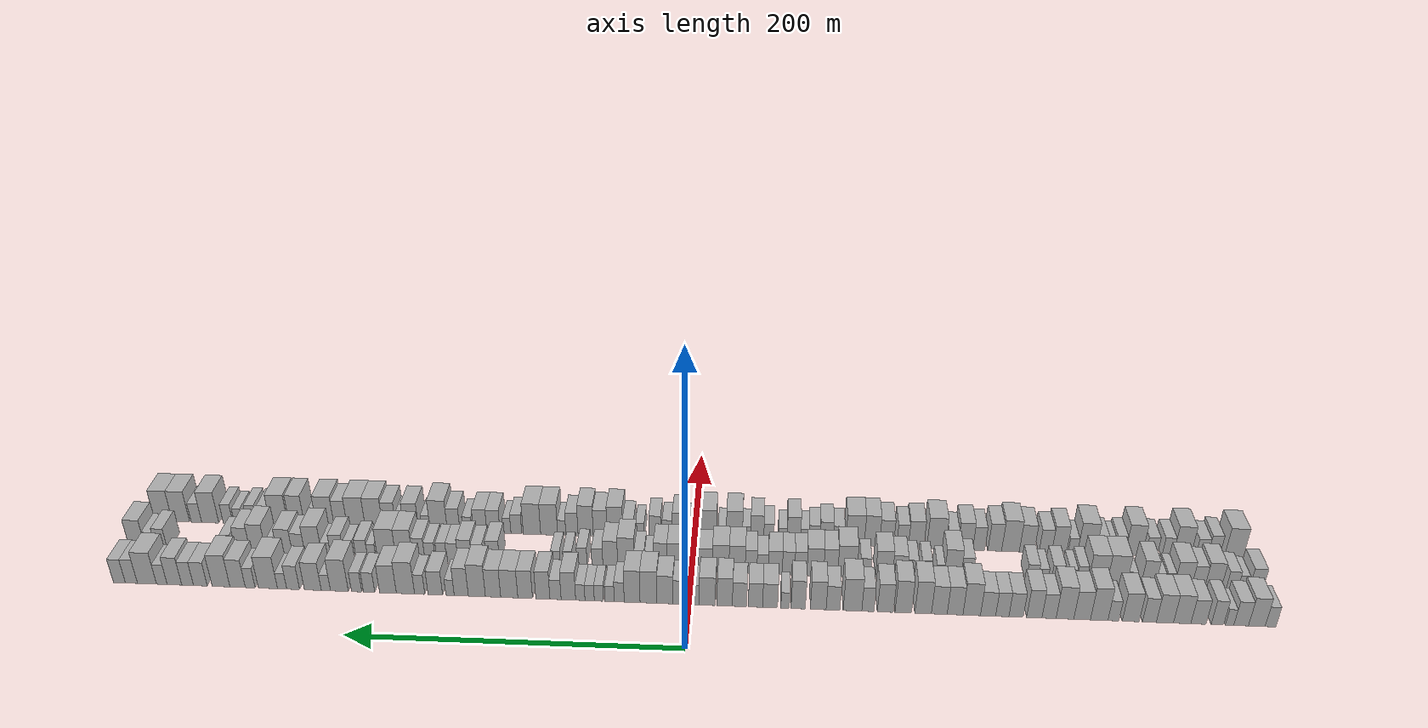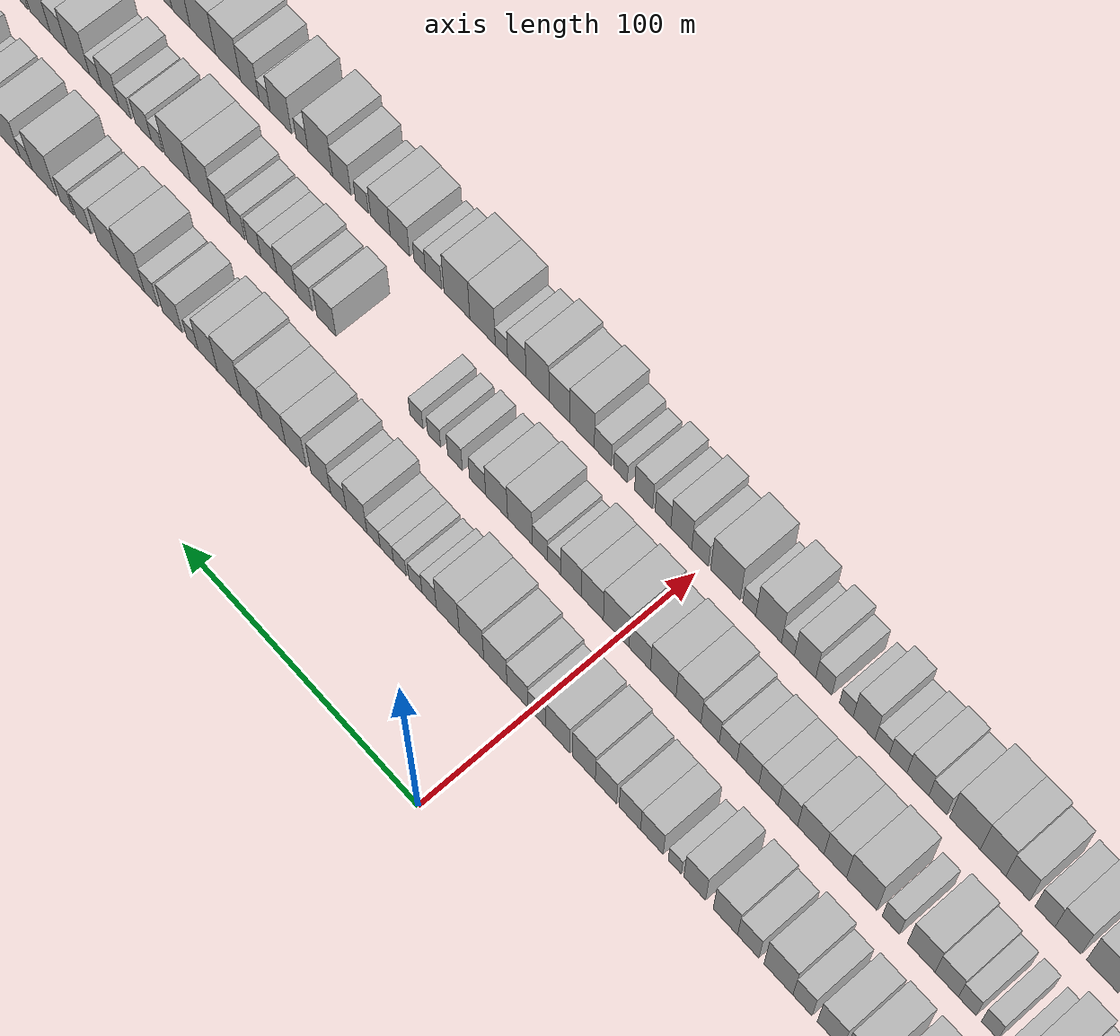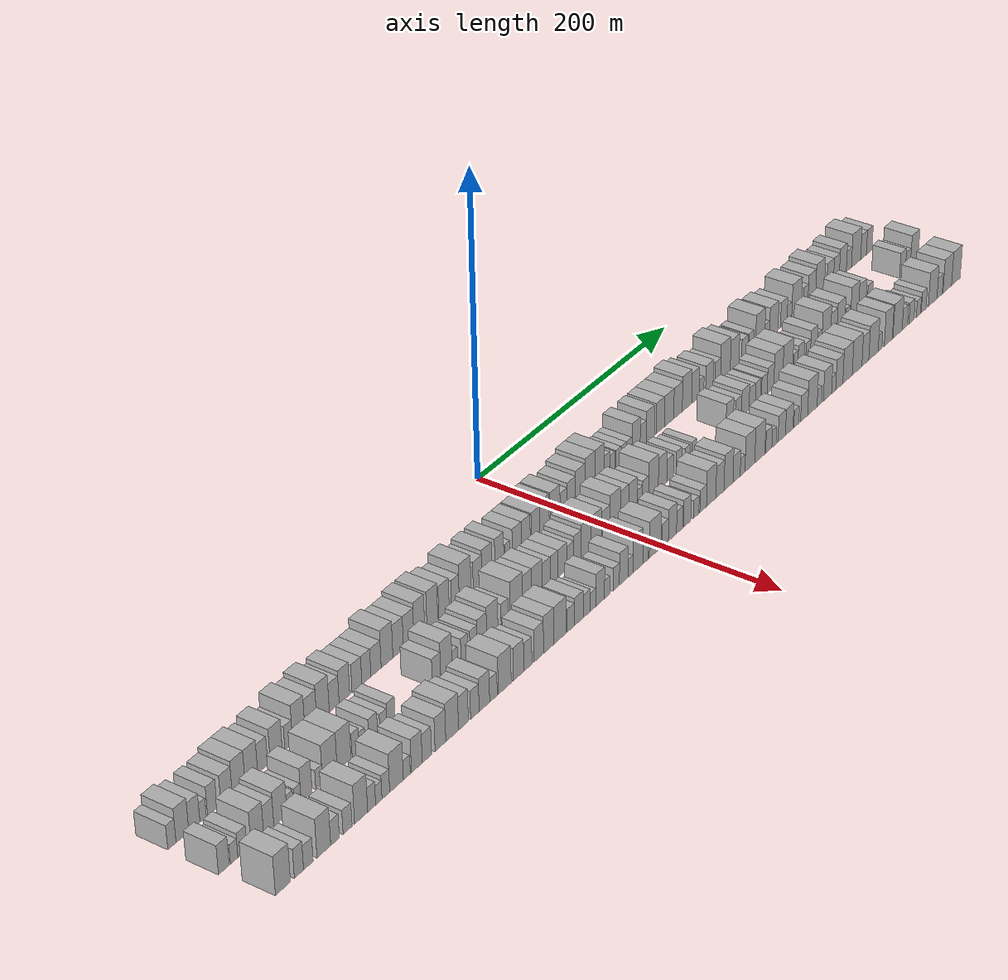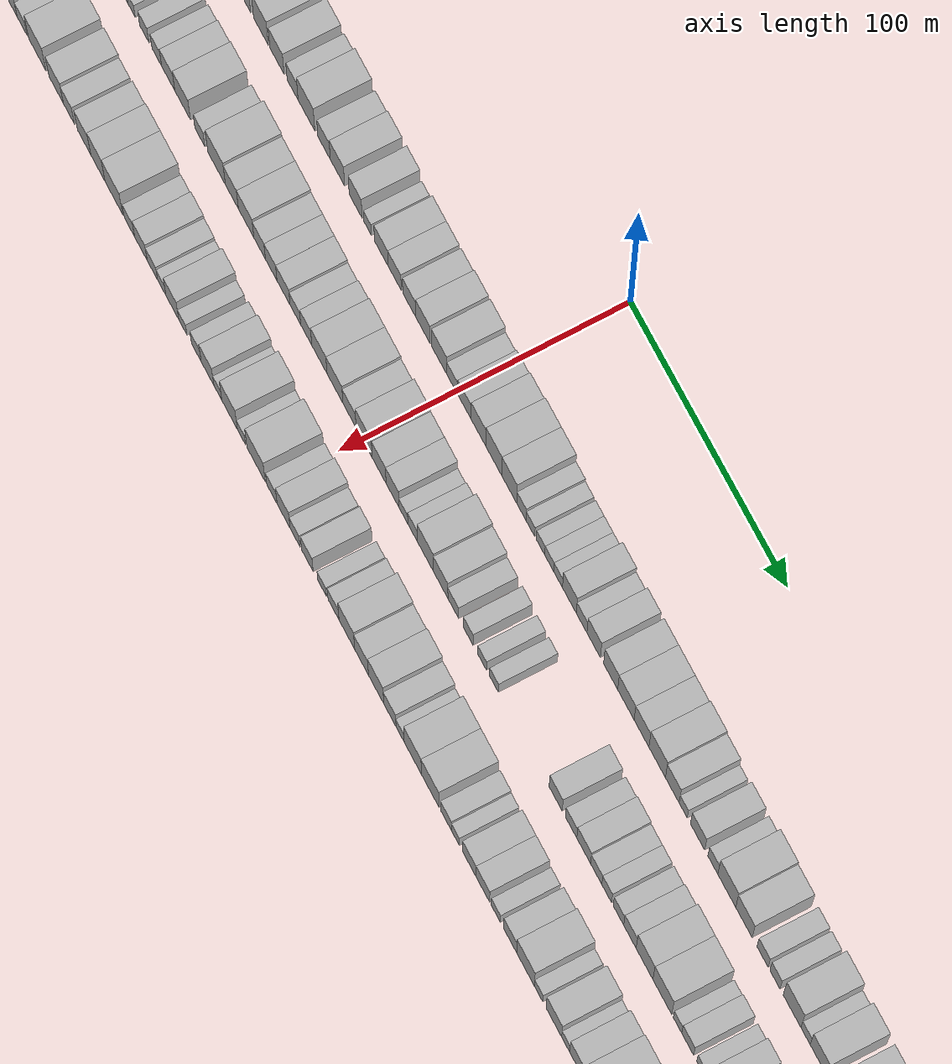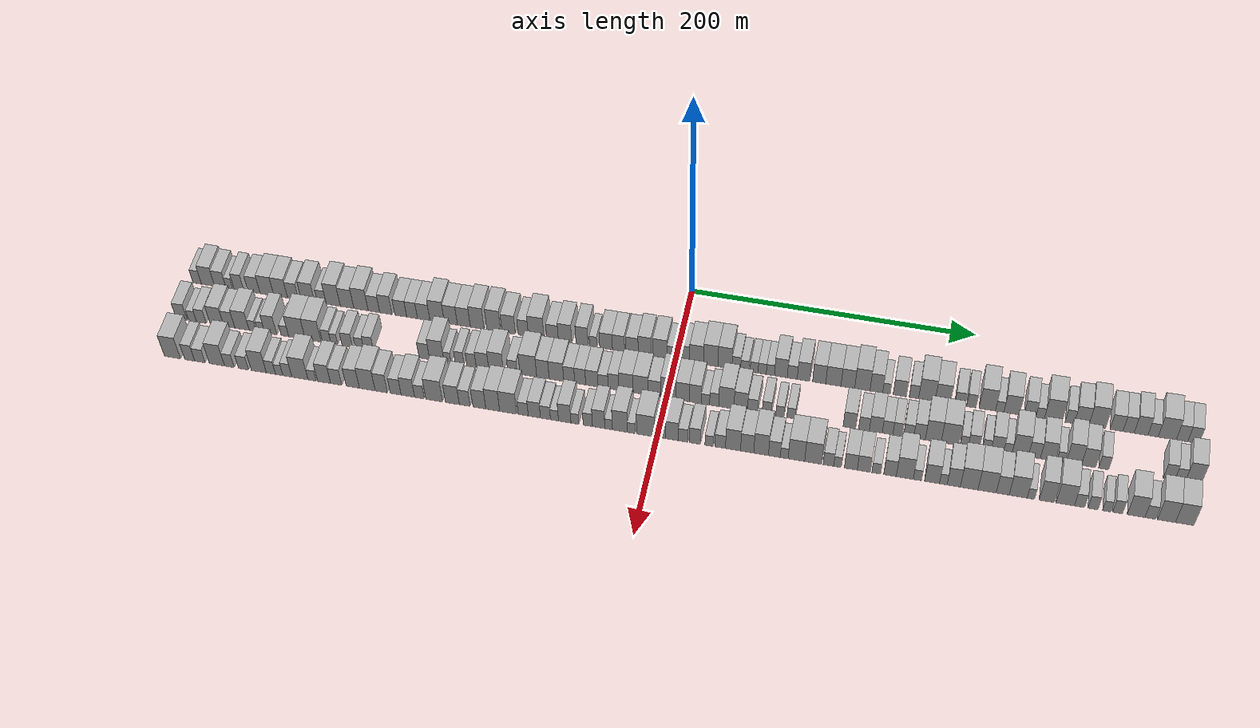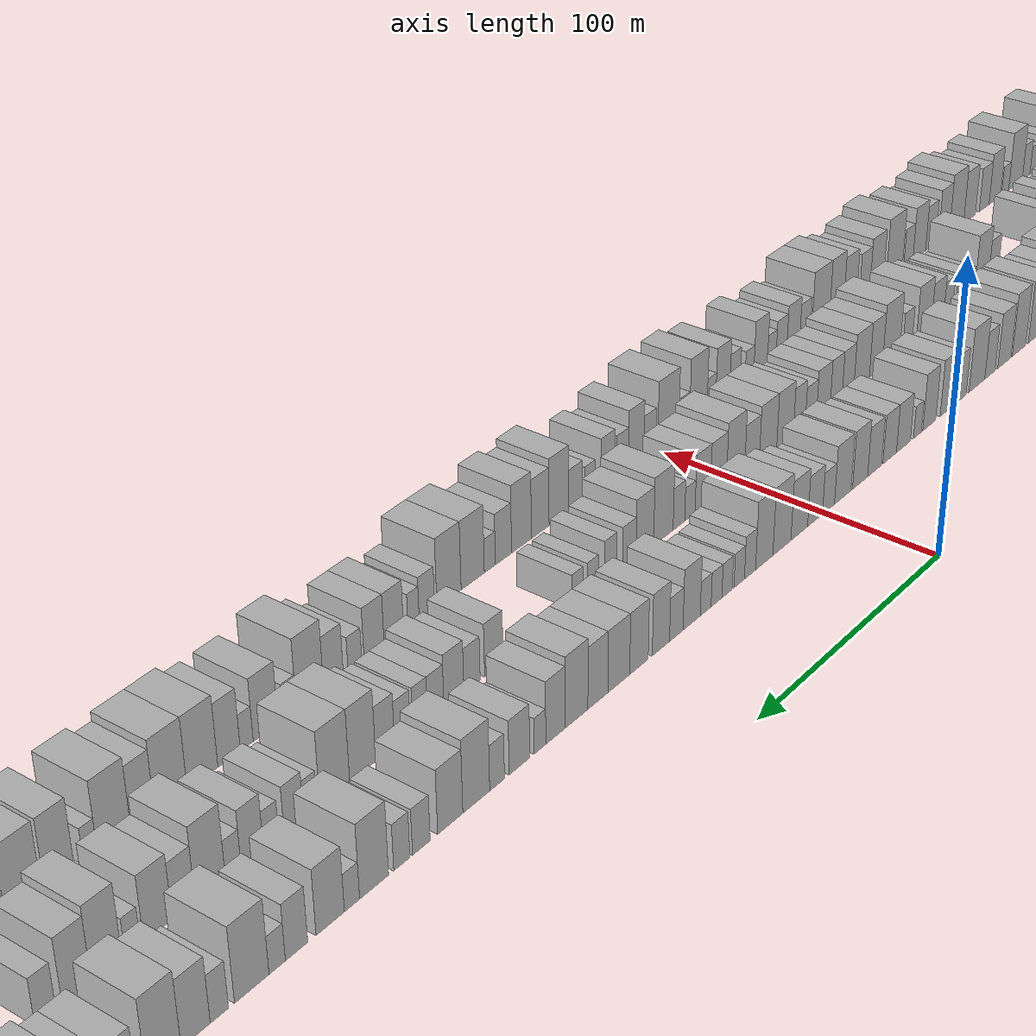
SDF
<sdf version="1.6">
 <world name="default">
  <scene>
   <sky><clouds><speed>12</speed></clouds></sky>
   <ambient>0.4 0.4 0.4 1</ambient>
   <background>0.7 0.7 0.7 1</background>
   <shadows>1</shadows>
  </scene>
  <gravity>0 0 -9.8066</gravity>
  <magnetic_field>6e-06 2.3e-05 -4.2e-05</magnetic_field>
  <physics default="0" name="default_physics" type="ode">
   <ode>
    <solver>
     <type>quick</type>
     <iters>10</iters>
     <sor>1.0</sor>
     <use_dynamic_moi_rescaling>0</use_dynamic_moi_rescaling>
    </solver>
    <constraints>
     <cfm>0</cfm>
     <erp>0.2</erp>
     <contact_max_correcting_vel>100</contact_max_correcting_vel>
     <contact_surface_layer>0.001</contact_surface_layer>
    </constraints>
   </ode>
   <max_step_size>0.004</max_step_size>
   <real_time_factor>1</real_time_factor>
   <real_time_update_rate>250</real_time_update_rate>
  </physics>
  <light name="sun" type="directional">
   <pose>0 0 10 0 0 0</pose>
   <diffuse>0.8 0.8 0.8 1</diffuse>
   <specular>0.2 0.2 0.2 1</specular>
   <attenuation>
    <range>1000</range>
    <constant>0.9</constant>
    <linear>0.01</linear>
    <quadratic>0.001</quadratic>
   </attenuation>
   <direction>-0.5 0.1 -0.9</direction>
  </light>
  <model name="building_1">
   <static>1</static>
   <pose>50.0000 -343.8874 0 0.000000 0.000000 0.000000</pose>
   <link name="link">
    <pose>0 0 7.50 0 0 0</pose>
    <collision name="collision"><geometry><box><size>20.0000 6.2253 15.0000</size></box></geometry></collision>
    <visual name="visual">
     <cast_shadows>0</cast_shadows>
     <geometry><box><size>20.0000 6.2253 15.0000</size></box></geometry>
     <material>
      <script>
       <uri>model://HANNAS_wall/materials/scripts</uri>
       <uri>model://HANNAS_wall/materials/textures</uri>
       <name>vrc/HANNAS_wall</name>
      </script>
     </material>
    </visual>
   </link>
  </model>
  <model name="building_2">
   <static>1</static>
   <pose>50.0000 -335.9303 0 0.000000 0.000000 0.000000</pose>
   <link name="link">
    <pose>0 0 10.50 0 0 0</pose>
    <collision name="collision"><geometry><box><size>20.0000 9.6890 21.0000</size></box></geometry></collision>
    <visual name="visual">
     <cast_shadows>0</cast_shadows>
     <geometry><box><size>20.0000 9.6890 21.0000</size></box></geometry>
     <material>
      <script>
       <uri>model://HANNAS_wall/materials/scripts</uri>
       <uri>model://HANNAS_wall/materials/textures</uri>
       <name>vrc/HANNAS_wall</name>
      </script>
     </material>
    </visual>
   </link>
  </model>
  <model name="building_3">
   <static>1</static>
   <pose>50.0000 -326.8503 0 0.000000 0.000000 0.000000</pose>
   <link name="link">
    <pose>0 0 9.00 0 0 0</pose>
    <collision name="collision"><geometry><box><size>20.0000 8.4710 18.0000</size></box></geometry></collision>
    <visual name="visual">
     <cast_shadows>0</cast_shadows>
     <geometry><box><size>20.0000 8.4710 18.0000</size></box></geometry>
     <material>
      <script>
       <uri>model://HANNAS_wall/materials/scripts</uri>
       <uri>model://HANNAS_wall/materials/textures</uri>
       <name>vrc/HANNAS_wall</name>
      </script>
     </material>
    </visual>
   </link>
  </model>
  <model name="building_4">
   <static>1</static>
   <pose>50.0000 -320.1682 0 0.000000 0.000000 0.000000</pose>
   <link name="link">
    <pose>0 0 6.00 0 0 0</pose>
    <collision name="collision"><geometry><box><size>20.0000 4.8932 12.0000</size></box></geometry></collision>
    <visual name="visual">
     <cast_shadows>0</cast_shadows>
     <geometry><box><size>20.0000 4.8932 12.0000</size></box></geometry>
     <material>
      <script>
       <uri>model://HANNAS_wall/materials/scripts</uri>
       <uri>model://HANNAS_wall/materials/textures</uri>
       <name>vrc/HANNAS_wall</name>
      </script>
     </material>
    </visual>
   </link>
  </model>
  <model name="building_5">
   <static>1</static>
   <pose>50.0000 -313.0852 0 0.000000 0.000000 0.000000</pose>
   <link name="link">
    <pose>0 0 9.00 0 0 0</pose>
    <collision name="collision"><geometry><box><size>20.0000 7.2727 18.0000</size></box></geometry></collision>
    <visual name="visual">
     <cast_shadows>0</cast_shadows>
     <geometry><box><size>20.0000 7.2727 18.0000</size></box></geometry>
     <material>
      <script>
       <uri>model://HANNAS_wall/materials/scripts</uri>
       <uri>model://HANNAS_wall/materials/textures</uri>
       <name>vrc/HANNAS_wall</name>
      </script>
     </material>
    </visual>
   </link>
  </model>
  <model name="building_6">
   <static>1</static>
   <pose>50.0000 -302.0077 0 0.000000 0.000000 0.000000</pose>
   <link name="link">
    <pose>0 0 9.00 0 0 0</pose>
    <collision name="collision"><geometry><box><size>20.0000 8.8823 18.0000</size></box></geometry></collision>
    <visual name="visual">
     <cast_shadows>0</cast_shadows>
     <geometry><box><size>20.0000 8.8823 18.0000</size></box></geometry>
     <material>
      <script>
       <uri>model://HANNAS_wall/materials/scripts</uri>
       <uri>model://HANNAS_wall/materials/textures</uri>
       <name>vrc/HANNAS_wall</name>
      </script>
     </material>
    </visual>
   </link>
  </model>
  <model name="building_7">
   <static>1</static>
   <pose>50.0000 -292.5127 0 0.000000 0.000000 0.000000</pose>
   <link name="link">
    <pose>0 0 10.50 0 0 0</pose>
    <collision name="collision"><geometry><box><size>20.0000 10.1076 21.0000</size></box></geometry></collision>
    <visual name="visual">
     <cast_shadows>0</cast_shadows>
     <geometry><box><size>20.0000 10.1076 21.0000</size></box></geometry>
     <material>
      <script>
       <uri>model://HANNAS_wall/materials/scripts</uri>
       <uri>model://HANNAS_wall/materials/textures</uri>
       <name>vrc/HANNAS_wall</name>
      </script>
     </material>
    </visual>
   </link>
  </model>
  <model name="building_8">
   <static>1</static>
   <pose>50.0000 -282.4507 0 0.000000 0.000000 0.000000</pose>
   <link name="link">
    <pose>0 0 10.50 0 0 0</pose>
    <collision name="collision"><geometry><box><size>20.0000 10.0166 21.0000</size></box></geometry></collision>
    <visual name="visual">
     <cast_shadows>0</cast_shadows>
     <geometry><box><size>20.0000 10.0166 21.0000</size></box></geometry>
     <material>
      <script>
       <uri>model://HANNAS_wall/materials/scripts</uri>
       <uri>model://HANNAS_wall/materials/textures</uri>
       <name>vrc/HANNAS_wall</name>
      </script>
     </material>
    </visual>
   </link>
  </model>
  <model name="building_9">
   <static>1</static>
   <pose>50.0000 -273.4089 0 0.000000 0.000000 0.000000</pose>
   <link name="link">
    <pose>0 0 9.00 0 0 0</pose>
    <collision name="collision"><geometry><box><size>20.0000 8.0670 18.0000</size></box></geometry></collision>
    <visual name="visual">
     <cast_shadows>0</cast_shadows>
     <geometry><box><size>20.0000 8.0670 18.0000</size></box></geometry>
     <material>
      <script>
       <uri>model://HANNAS_wall/materials/scripts</uri>
       <uri>model://HANNAS_wall/materials/textures</uri>
       <name>vrc/HANNAS_wall</name>
      </script>
     </material>
    </visual>
   </link>
  </model>
  <model name="building_10">
   <static>1</static>
   <pose>50.0000 -262.4600 0 0.000000 0.000000 0.000000</pose>
   <link name="link">
    <pose>0 0 10.50 0 0 0</pose>
    <collision name="collision"><geometry><box><size>20.0000 9.8308 21.0000</size></box></geometry></collision>
    <visual name="visual">
     <cast_shadows>0</cast_shadows>
     <geometry><box><size>20.0000 9.8308 21.0000</size></box></geometry>
     <material>
      <script>
       <uri>model://HANNAS_wall/materials/scripts</uri>
       <uri>model://HANNAS_wall/materials/textures</uri>
       <name>vrc/HANNAS_wall</name>
      </script>
     </material>
    </visual>
   </link>
  </model>
  <model name="building_11">
   <static>1</static>
   <pose>50.0000 -252.3469 0 0.000000 0.000000 0.000000</pose>
   <link name="link">
    <pose>0 0 7.50 0 0 0</pose>
    <collision name="collision"><geometry><box><size>20.0000 6.3953 15.0000</size></box></geometry></collision>
    <visual name="visual">
     <cast_shadows>0</cast_shadows>
     <geometry><box><size>20.0000 6.3953 15.0000</size></box></geometry>
     <material>
      <script>
       <uri>model://HANNAS_wall/materials/scripts</uri>
       <uri>model://HANNAS_wall/materials/textures</uri>
       <name>vrc/HANNAS_wall</name>
      </script>
     </material>
    </visual>
   </link>
  </model>
  <model name="building_12">
   <static>1</static>
   <pose>50.0000 -244.0299 0 0.000000 0.000000 0.000000</pose>
   <link name="link">
    <pose>0 0 12.00 0 0 0</pose>
    <collision name="collision"><geometry><box><size>20.0000 10.2387 24.0000</size></box></geometry></collision>
    <visual name="visual">
     <cast_shadows>0</cast_shadows>
     <geometry><box><size>20.0000 10.2387 24.0000</size></box></geometry>
     <material>
      <script>
       <uri>model://HANNAS_wall/materials/scripts</uri>
       <uri>model://HANNAS_wall/materials/textures</uri>
       <name>vrc/HANNAS_wall</name>
      </script>
     </material>
    </visual>
   </link>
  </model>
  <model name="building_13">
   <static>1</static>
   <pose>50.0000 -234.0104 0 0.000000 0.000000 0.000000</pose>
   <link name="link">
    <pose>0 0 10.50 0 0 0</pose>
    <collision name="collision"><geometry><box><size>20.0000 9.8004 21.0000</size></box></geometry></collision>
    <visual name="visual">
     <cast_shadows>0</cast_shadows>
     <geometry><box><size>20.0000 9.8004 21.0000</size></box></geometry>
     <material>
      <script>
       <uri>model://HANNAS_wall/materials/scripts</uri>
       <uri>model://HANNAS_wall/materials/textures</uri>
       <name>vrc/HANNAS_wall</name>
      </script>
     </material>
    </visual>
   </link>
  </model>
  <model name="building_14">
   <static>1</static>
   <pose>50.0000 -223.8945 0 0.000000 0.000000 0.000000</pose>
   <link name="link">
    <pose>0 0 12.00 0 0 0</pose>
    <collision name="collision"><geometry><box><size>20.0000 10.4314 24.0000</size></box></geometry></collision>
    <visual name="visual">
     <cast_shadows>0</cast_shadows>
     <geometry><box><size>20.0000 10.4314 24.0000</size></box></geometry>
     <material>
      <script>
       <uri>model://HANNAS_wall/materials/scripts</uri>
       <uri>model://HANNAS_wall/materials/textures</uri>
       <name>vrc/HANNAS_wall</name>
      </script>
     </material>
    </visual>
   </link>
  </model>
  <model name="building_15">
   <static>1</static>
   <pose>50.0000 -214.5251 0 0.000000 0.000000 0.000000</pose>
   <link name="link">
    <pose>0 0 9.00 0 0 0</pose>
    <collision name="collision"><geometry><box><size>20.0000 8.3074 18.0000</size></box></geometry></collision>
    <visual name="visual">
     <cast_shadows>0</cast_shadows>
     <geometry><box><size>20.0000 8.3074 18.0000</size></box></geometry>
     <material>
      <script>
       <uri>model://HANNAS_wall/materials/scripts</uri>
       <uri>model://HANNAS_wall/materials/textures</uri>
       <name>vrc/HANNAS_wall</name>
      </script>
     </material>
    </visual>
   </link>
  </model>
  <model name="building_16">
   <static>1</static>
   <pose>50.0000 -205.8748 0 0.000000 0.000000 0.000000</pose>
   <link name="link">
    <pose>0 0 10.50 0 0 0</pose>
    <collision name="collision"><geometry><box><size>20.0000 8.9932 21.0000</size></box></geometry></collision>
    <visual name="visual">
     <cast_shadows>0</cast_shadows>
     <geometry><box><size>20.0000 8.9932 21.0000</size></box></geometry>
     <material>
      <script>
       <uri>model://HANNAS_wall/materials/scripts</uri>
       <uri>model://HANNAS_wall/materials/textures</uri>
       <name>vrc/HANNAS_wall</name>
      </script>
     </material>
    </visual>
   </link>
  </model>
  <model name="building_17">
   <static>1</static>
   <pose>50.0000 -195.1468 0 0.000000 0.000000 0.000000</pose>
   <link name="link">
    <pose>0 0 9.00 0 0 0</pose>
    <collision name="collision"><geometry><box><size>20.0000 8.4629 18.0000</size></box></geometry></collision>
    <visual name="visual">
     <cast_shadows>0</cast_shadows>
     <geometry><box><size>20.0000 8.4629 18.0000</size></box></geometry>
     <material>
      <script>
       <uri>model://HANNAS_wall/materials/scripts</uri>
       <uri>model://HANNAS_wall/materials/textures</uri>
       <name>vrc/HANNAS_wall</name>
      </script>
     </material>
    </visual>
   </link>
  </model>
  <model name="building_18">
   <static>1</static>
   <pose>50.0000 -187.0076 0 0.000000 0.000000 0.000000</pose>
   <link name="link">
    <pose>0 0 9.00 0 0 0</pose>
    <collision name="collision"><geometry><box><size>20.0000 7.8156 18.0000</size></box></geometry></collision>
    <visual name="visual">
     <cast_shadows>0</cast_shadows>
     <geometry><box><size>20.0000 7.8156 18.0000</size></box></geometry>
     <material>
      <script>
       <uri>model://HANNAS_wall/materials/scripts</uri>
       <uri>model://HANNAS_wall/materials/textures</uri>
       <name>vrc/HANNAS_wall</name>
      </script>
     </material>
    </visual>
   </link>
  </model>
  <model name="building_19">
   <static>1</static>
   <pose>50.0000 -178.6172 0 0.000000 0.000000 0.000000</pose>
   <link name="link">
    <pose>0 0 9.00 0 0 0</pose>
    <collision name="collision"><geometry><box><size>20.0000 8.9651 18.0000</size></box></geometry></collision>
    <visual name="visual">
     <cast_shadows>0</cast_shadows>
     <geometry><box><size>20.0000 8.9651 18.0000</size></box></geometry>
     <material>
      <script>
       <uri>model://HANNAS_wall/materials/scripts</uri>
       <uri>model://HANNAS_wall/materials/textures</uri>
       <name>vrc/HANNAS_wall</name>
      </script>
     </material>
    </visual>
   </link>
  </model>
  <model name="building_20">
   <static>1</static>
   <pose>50.0000 -168.9463 0 0.000000 0.000000 0.000000</pose>
   <link name="link">
    <pose>0 0 12.00 0 0 0</pose>
    <collision name="collision"><geometry><box><size>20.0000 10.3767 24.0000</size></box></geometry></collision>
    <visual name="visual">
     <cast_shadows>0</cast_shadows>
     <geometry><box><size>20.0000 10.3767 24.0000</size></box></geometry>
     <material>
      <script>
       <uri>model://HANNAS_wall/materials/scripts</uri>
       <uri>model://HANNAS_wall/materials/textures</uri>
       <name>vrc/HANNAS_wall</name>
      </script>
     </material>
    </visual>
   </link>
  </model>
  <model name="building_21">
   <static>1</static>
   <pose>50.0000 -159.0779 0 0.000000 0.000000 0.000000</pose>
   <link name="link">
    <pose>0 0 10.50 0 0 0</pose>
    <collision name="collision"><geometry><box><size>20.0000 9.3601 21.0000</size></box></geometry></collision>
    <visual name="visual">
     <cast_shadows>0</cast_shadows>
     <geometry><box><size>20.0000 9.3601 21.0000</size></box></geometry>
     <material>
      <script>
       <uri>model://HANNAS_wall/materials/scripts</uri>
       <uri>model://HANNAS_wall/materials/textures</uri>
       <name>vrc/HANNAS_wall</name>
      </script>
     </material>
    </visual>
   </link>
  </model>
  <model name="building_22">
   <static>1</static>
   <pose>50.0000 -149.7265 0 0.000000 0.000000 0.000000</pose>
   <link name="link">
    <pose>0 0 10.50 0 0 0</pose>
    <collision name="collision"><geometry><box><size>20.0000 9.3427 21.0000</size></box></geometry></collision>
    <visual name="visual">
     <cast_shadows>0</cast_shadows>
     <geometry><box><size>20.0000 9.3427 21.0000</size></box></geometry>
     <material>
      <script>
       <uri>model://HANNAS_wall/materials/scripts</uri>
       <uri>model://HANNAS_wall/materials/textures</uri>
       <name>vrc/HANNAS_wall</name>
      </script>
     </material>
    </visual>
   </link>
  </model>
  <model name="building_23">
   <static>1</static>
   <pose>50.0000 -140.1592 0 0.000000 0.000000 0.000000</pose>
   <link name="link">
    <pose>0 0 12.00 0 0 0</pose>
    <collision name="collision"><geometry><box><size>20.0000 9.7919 24.0000</size></box></geometry></collision>
    <visual name="visual">
     <cast_shadows>0</cast_shadows>
     <geometry><box><size>20.0000 9.7919 24.0000</size></box></geometry>
     <material>
      <script>
       <uri>model://HANNAS_wall/materials/scripts</uri>
       <uri>model://HANNAS_wall/materials/textures</uri>
       <name>vrc/HANNAS_wall</name>
      </script>
     </material>
    </visual>
   </link>
  </model>
  <model name="building_24">
   <static>1</static>
   <pose>50.0000 -128.3486 0 0.000000 0.000000 0.000000</pose>
   <link name="link">
    <pose>0 0 12.00 0 0 0</pose>
    <collision name="collision"><geometry><box><size>20.0000 9.8294 24.0000</size></box></geometry></collision>
    <visual name="visual">
     <cast_shadows>0</cast_shadows>
     <geometry><box><size>20.0000 9.8294 24.0000</size></box></geometry>
     <material>
      <script>
       <uri>model://HANNAS_wall/materials/scripts</uri>
       <uri>model://HANNAS_wall/materials/textures</uri>
       <name>vrc/HANNAS_wall</name>
      </script>
     </material>
    </visual>
   </link>
  </model>
  <model name="building_25">
   <static>1</static>
   <pose>50.0000 -117.6732 0 0.000000 0.000000 0.000000</pose>
   <link name="link">
    <pose>0 0 10.50 0 0 0</pose>
    <collision name="collision"><geometry><box><size>20.0000 9.5214 21.0000</size></box></geometry></collision>
    <visual name="visual">
     <cast_shadows>0</cast_shadows>
     <geometry><box><size>20.0000 9.5214 21.0000</size></box></geometry>
     <material>
      <script>
       <uri>model://HANNAS_wall/materials/scripts</uri>
       <uri>model://HANNAS_wall/materials/textures</uri>
       <name>vrc/HANNAS_wall</name>
      </script>
     </material>
    </visual>
   </link>
  </model>
  <model name="building_26">
   <static>1</static>
   <pose>50.0000 -107.2792 0 0.000000 0.000000 0.000000</pose>
   <link name="link">
    <pose>0 0 9.00 0 0 0</pose>
    <collision name="collision"><geometry><box><size>20.0000 7.2665 18.0000</size></box></geometry></collision>
    <visual name="visual">
     <cast_shadows>0</cast_shadows>
     <geometry><box><size>20.0000 7.2665 18.0000</size></box></geometry>
     <material>
      <script>
       <uri>model://HANNAS_wall/materials/scripts</uri>
       <uri>model://HANNAS_wall/materials/textures</uri>
       <name>vrc/HANNAS_wall</name>
      </script>
     </material>
    </visual>
   </link>
  </model>
  <model name="building_27">
   <static>1</static>
   <pose>50.0000 -98.1039 0 0.000000 0.000000 0.000000</pose>
   <link name="link">
    <pose>0 0 12.00 0 0 0</pose>
    <collision name="collision"><geometry><box><size>20.0000 11.0840 24.0000</size></box></geometry></collision>
    <visual name="visual">
     <cast_shadows>0</cast_shadows>
     <geometry><box><size>20.0000 11.0840 24.0000</size></box></geometry>
     <material>
      <script>
       <uri>model://HANNAS_wall/materials/scripts</uri>
       <uri>model://HANNAS_wall/materials/textures</uri>
       <name>vrc/HANNAS_wall</name>
      </script>
     </material>
    </visual>
   </link>
  </model>
  <model name="building_28">
   <static>1</static>
   <pose>50.0000 -86.4578 0 0.000000 0.000000 0.000000</pose>
   <link name="link">
    <pose>0 0 9.00 0 0 0</pose>
    <collision name="collision"><geometry><box><size>20.0000 8.2081 18.0000</size></box></geometry></collision>
    <visual name="visual">
     <cast_shadows>0</cast_shadows>
     <geometry><box><size>20.0000 8.2081 18.0000</size></box></geometry>
     <material>
      <script>
       <uri>model://HANNAS_wall/materials/scripts</uri>
       <uri>model://HANNAS_wall/materials/textures</uri>
       <name>vrc/HANNAS_wall</name>
      </script>
     </material>
    </visual>
   </link>
  </model>
  <model name="building_29">
   <static>1</static>
   <pose>50.0000 -77.6245 0 0.000000 0.000000 0.000000</pose>
   <link name="link">
    <pose>0 0 10.50 0 0 0</pose>
    <collision name="collision"><geometry><box><size>20.0000 9.4585 21.0000</size></box></geometry></collision>
    <visual name="visual">
     <cast_shadows>0</cast_shadows>
     <geometry><box><size>20.0000 9.4585 21.0000</size></box></geometry>
     <material>
      <script>
       <uri>model://HANNAS_wall/materials/scripts</uri>
       <uri>model://HANNAS_wall/materials/textures</uri>
       <name>vrc/HANNAS_wall</name>
      </script>
     </material>
    </visual>
   </link>
  </model>
  <model name="building_30">
   <static>1</static>
   <pose>50.0000 -65.6225 0 0.000000 0.000000 0.000000</pose>
   <link name="link">
    <pose>0 0 10.50 0 0 0</pose>
    <collision name="collision"><geometry><box><size>20.0000 8.5455 21.0000</size></box></geometry></collision>
    <visual name="visual">
     <cast_shadows>0</cast_shadows>
     <geometry><box><size>20.0000 8.5455 21.0000</size></box></geometry>
     <material>
      <script>
       <uri>model://HANNAS_wall/materials/scripts</uri>
       <uri>model://HANNAS_wall/materials/textures</uri>
       <name>vrc/HANNAS_wall</name>
      </script>
     </material>
    </visual>
   </link>
  </model>
  <model name="building_31">
   <static>1</static>
   <pose>50.0000 -57.7851 0 0.000000 0.000000 0.000000</pose>
   <link name="link">
    <pose>0 0 6.00 0 0 0</pose>
    <collision name="collision"><geometry><box><size>20.0000 5.1292 12.0000</size></box></geometry></collision>
    <visual name="visual">
     <cast_shadows>0</cast_shadows>
     <geometry><box><size>20.0000 5.1292 12.0000</size></box></geometry>
     <material>
      <script>
       <uri>model://HANNAS_wall/materials/scripts</uri>
       <uri>model://HANNAS_wall/materials/textures</uri>
       <name>vrc/HANNAS_wall</name>
      </script>
     </material>
    </visual>
   </link>
  </model>
  <model name="building_32">
   <static>1</static>
   <pose>50.0000 -48.7332 0 0.000000 0.000000 0.000000</pose>
   <link name="link">
    <pose>0 0 9.00 0 0 0</pose>
    <collision name="collision"><geometry><box><size>20.0000 8.9747 18.0000</size></box></geometry></collision>
    <visual name="visual">
     <cast_shadows>0</cast_shadows>
     <geometry><box><size>20.0000 8.9747 18.0000</size></box></geometry>
     <material>
      <script>
       <uri>model://HANNAS_wall/materials/scripts</uri>
       <uri>model://HANNAS_wall/materials/textures</uri>
       <name>vrc/HANNAS_wall</name>
      </script>
     </material>
    </visual>
   </link>
  </model>
  <model name="building_33">
   <static>1</static>
   <pose>50.0000 -39.9709 0 0.000000 0.000000 0.000000</pose>
   <link name="link">
    <pose>0 0 9.00 0 0 0</pose>
    <collision name="collision"><geometry><box><size>20.0000 8.5499 18.0000</size></box></geometry></collision>
    <visual name="visual">
     <cast_shadows>0</cast_shadows>
     <geometry><box><size>20.0000 8.5499 18.0000</size></box></geometry>
     <material>
      <script>
       <uri>model://HANNAS_wall/materials/scripts</uri>
       <uri>model://HANNAS_wall/materials/textures</uri>
       <name>vrc/HANNAS_wall</name>
      </script>
     </material>
    </visual>
   </link>
  </model>
  <model name="building_34">
   <static>1</static>
   <pose>50.0000 -30.4042 0 0.000000 0.000000 0.000000</pose>
   <link name="link">
    <pose>0 0 9.00 0 0 0</pose>
    <collision name="collision"><geometry><box><size>20.0000 8.5835 18.0000</size></box></geometry></collision>
    <visual name="visual">
     <cast_shadows>0</cast_shadows>
     <geometry><box><size>20.0000 8.5835 18.0000</size></box></geometry>
     <material>
      <script>
       <uri>model://HANNAS_wall/materials/scripts</uri>
       <uri>model://HANNAS_wall/materials/textures</uri>
       <name>vrc/HANNAS_wall</name>
      </script>
     </material>
    </visual>
   </link>
  </model>
  <model name="building_35">
   <static>1</static>
   <pose>50.0000 -21.4919 0 0.000000 0.000000 0.000000</pose>
   <link name="link">
    <pose>0 0 10.50 0 0 0</pose>
    <collision name="collision"><geometry><box><size>20.0000 9.2410 21.0000</size></box></geometry></collision>
    <visual name="visual">
     <cast_shadows>0</cast_shadows>
     <geometry><box><size>20.0000 9.2410 21.0000</size></box></geometry>
     <material>
      <script>
       <uri>model://HANNAS_wall/materials/scripts</uri>
       <uri>model://HANNAS_wall/materials/textures</uri>
       <name>vrc/HANNAS_wall</name>
      </script>
     </material>
    </visual>
   </link>
  </model>
  <model name="building_36">
   <static>1</static>
   <pose>50.0000 -10.9206 0 0.000000 0.000000 0.000000</pose>
   <link name="link">
    <pose>0 0 10.50 0 0 0</pose>
    <collision name="collision"><geometry><box><size>20.0000 9.9016 21.0000</size></box></geometry></collision>
    <visual name="visual">
     <cast_shadows>0</cast_shadows>
     <geometry><box><size>20.0000 9.9016 21.0000</size></box></geometry>
     <material>
      <script>
       <uri>model://HANNAS_wall/materials/scripts</uri>
       <uri>model://HANNAS_wall/materials/textures</uri>
       <name>vrc/HANNAS_wall</name>
      </script>
     </material>
    </visual>
   </link>
  </model>
  <model name="building_37">
   <static>1</static>
   <pose>50.0000 -2.4017 0 0.000000 0.000000 0.000000</pose>
   <link name="link">
    <pose>0 0 7.50 0 0 0</pose>
    <collision name="collision"><geometry><box><size>20.0000 7.1364 15.0000</size></box></geometry></collision>
    <visual name="visual">
     <cast_shadows>0</cast_shadows>
     <geometry><box><size>20.0000 7.1364 15.0000</size></box></geometry>
     <material>
      <script>
       <uri>model://HANNAS_wall/materials/scripts</uri>
       <uri>model://HANNAS_wall/materials/textures</uri>
       <name>vrc/HANNAS_wall</name>
      </script>
     </material>
    </visual>
   </link>
  </model>
  <model name="building_38">
   <static>1</static>
   <pose>50.0000 5.5079 0 0.000000 0.000000 0.000000</pose>
   <link name="link">
    <pose>0 0 9.00 0 0 0</pose>
    <collision name="collision"><geometry><box><size>20.0000 8.6827 18.0000</size></box></geometry></collision>
    <visual name="visual">
     <cast_shadows>0</cast_shadows>
     <geometry><box><size>20.0000 8.6827 18.0000</size></box></geometry>
     <material>
      <script>
       <uri>model://HANNAS_wall/materials/scripts</uri>
       <uri>model://HANNAS_wall/materials/textures</uri>
       <name>vrc/HANNAS_wall</name>
      </script>
     </material>
    </visual>
   </link>
  </model>
  <model name="building_39">
   <static>1</static>
   <pose>50.0000 14.6435 0 0.000000 0.000000 0.000000</pose>
   <link name="link">
    <pose>0 0 10.50 0 0 0</pose>
    <collision name="collision"><geometry><box><size>20.0000 9.5886 21.0000</size></box></geometry></collision>
    <visual name="visual">
     <cast_shadows>0</cast_shadows>
     <geometry><box><size>20.0000 9.5886 21.0000</size></box></geometry>
     <material>
      <script>
       <uri>model://HANNAS_wall/materials/scripts</uri>
       <uri>model://HANNAS_wall/materials/textures</uri>
       <name>vrc/HANNAS_wall</name>
      </script>
     </material>
    </visual>
   </link>
  </model>
  <model name="building_40">
   <static>1</static>
   <pose>50.0000 24.5207 0 0.000000 0.000000 0.000000</pose>
   <link name="link">
    <pose>0 0 12.00 0 0 0</pose>
    <collision name="collision"><geometry><box><size>20.0000 10.1659 24.0000</size></box></geometry></collision>
    <visual name="visual">
     <cast_shadows>0</cast_shadows>
     <geometry><box><size>20.0000 10.1659 24.0000</size></box></geometry>
     <material>
      <script>
       <uri>model://HANNAS_wall/materials/scripts</uri>
       <uri>model://HANNAS_wall/materials/textures</uri>
       <name>vrc/HANNAS_wall</name>
      </script>
     </material>
    </visual>
   </link>
  </model>
  <model name="building_41">
   <static>1</static>
   <pose>50.0000 34.4200 0 0.000000 0.000000 0.000000</pose>
   <link name="link">
    <pose>0 0 12.00 0 0 0</pose>
    <collision name="collision"><geometry><box><size>20.0000 9.6327 24.0000</size></box></geometry></collision>
    <visual name="visual">
     <cast_shadows>0</cast_shadows>
     <geometry><box><size>20.0000 9.6327 24.0000</size></box></geometry>
     <material>
      <script>
       <uri>model://HANNAS_wall/materials/scripts</uri>
       <uri>model://HANNAS_wall/materials/textures</uri>
       <name>vrc/HANNAS_wall</name>
      </script>
     </material>
    </visual>
   </link>
  </model>
  <model name="building_42">
   <static>1</static>
   <pose>50.0000 42.2608 0 0.000000 0.000000 0.000000</pose>
   <link name="link">
    <pose>0 0 7.50 0 0 0</pose>
    <collision name="collision"><geometry><box><size>20.0000 6.0489 15.0000</size></box></geometry></collision>
    <visual name="visual">
     <cast_shadows>0</cast_shadows>
     <geometry><box><size>20.0000 6.0489 15.0000</size></box></geometry>
     <material>
      <script>
       <uri>model://HANNAS_wall/materials/scripts</uri>
       <uri>model://HANNAS_wall/materials/textures</uri>
       <name>vrc/HANNAS_wall</name>
      </script>
     </material>
    </visual>
   </link>
  </model>
  <model name="building_43">
   <static>1</static>
   <pose>50.0000 48.0974 0 0.000000 0.000000 0.000000</pose>
   <link name="link">
    <pose>0 0 6.00 0 0 0</pose>
    <collision name="collision"><geometry><box><size>20.0000 5.6243 12.0000</size></box></geometry></collision>
    <visual name="visual">
     <cast_shadows>0</cast_shadows>
     <geometry><box><size>20.0000 5.6243 12.0000</size></box></geometry>
     <material>
      <script>
       <uri>model://HANNAS_wall/materials/scripts</uri>
       <uri>model://HANNAS_wall/materials/textures</uri>
       <name>vrc/HANNAS_wall</name>
      </script>
     </material>
    </visual>
   </link>
  </model>
  <model name="building_44">
   <static>1</static>
   <pose>50.0000 54.6362 0 0.000000 0.000000 0.000000</pose>
   <link name="link">
    <pose>0 0 6.00 0 0 0</pose>
    <collision name="collision"><geometry><box><size>20.0000 5.4533 12.0000</size></box></geometry></collision>
    <visual name="visual">
     <cast_shadows>0</cast_shadows>
     <geometry><box><size>20.0000 5.4533 12.0000</size></box></geometry>
     <material>
      <script>
       <uri>model://HANNAS_wall/materials/scripts</uri>
       <uri>model://HANNAS_wall/materials/textures</uri>
       <name>vrc/HANNAS_wall</name>
      </script>
     </material>
    </visual>
   </link>
  </model>
  <model name="building_45">
   <static>1</static>
   <pose>50.0000 60.2041 0 0.000000 0.000000 0.000000</pose>
   <link name="link">
    <pose>0 0 6.00 0 0 0</pose>
    <collision name="collision"><geometry><box><size>20.0000 5.6824 12.0000</size></box></geometry></collision>
    <visual name="visual">
     <cast_shadows>0</cast_shadows>
     <geometry><box><size>20.0000 5.6824 12.0000</size></box></geometry>
     <material>
      <script>
       <uri>model://HANNAS_wall/materials/scripts</uri>
       <uri>model://HANNAS_wall/materials/textures</uri>
       <name>vrc/HANNAS_wall</name>
      </script>
     </material>
    </visual>
   </link>
  </model>
  <model name="building_46">
   <static>1</static>
   <pose>50.0000 65.8773 0 0.000000 0.000000 0.000000</pose>
   <link name="link">
    <pose>0 0 6.00 0 0 0</pose>
    <collision name="collision"><geometry><box><size>20.0000 5.6639 12.0000</size></box></geometry></collision>
    <visual name="visual">
     <cast_shadows>0</cast_shadows>
     <geometry><box><size>20.0000 5.6639 12.0000</size></box></geometry>
     <material>
      <script>
       <uri>model://HANNAS_wall/materials/scripts</uri>
       <uri>model://HANNAS_wall/materials/textures</uri>
       <name>vrc/HANNAS_wall</name>
      </script>
     </material>
    </visual>
   </link>
  </model>
  <model name="building_47">
   <static>1</static>
   <pose>50.0000 73.1357 0 0.000000 0.000000 0.000000</pose>
   <link name="link">
    <pose>0 0 10.50 0 0 0</pose>
    <collision name="collision"><geometry><box><size>20.0000 8.8529 21.0000</size></box></geometry></collision>
    <visual name="visual">
     <cast_shadows>0</cast_shadows>
     <geometry><box><size>20.0000 8.8529 21.0000</size></box></geometry>
     <material>
      <script>
       <uri>model://HANNAS_wall/materials/scripts</uri>
       <uri>model://HANNAS_wall/materials/textures</uri>
       <name>vrc/HANNAS_wall</name>
      </script>
     </material>
    </visual>
   </link>
  </model>
  <model name="building_48">
   <static>1</static>
   <pose>50.0000 80.9714 0 0.000000 0.000000 0.000000</pose>
   <link name="link">
    <pose>0 0 7.50 0 0 0</pose>
    <collision name="collision"><geometry><box><size>20.0000 6.8185 15.0000</size></box></geometry></collision>
    <visual name="visual">
     <cast_shadows>0</cast_shadows>
     <geometry><box><size>20.0000 6.8185 15.0000</size></box></geometry>
     <material>
      <script>
       <uri>model://HANNAS_wall/materials/scripts</uri>
       <uri>model://HANNAS_wall/materials/textures</uri>
       <name>vrc/HANNAS_wall</name>
      </script>
     </material>
    </visual>
   </link>
  </model>
  <model name="building_49">
   <static>1</static>
   <pose>50.0000 88.6767 0 0.000000 0.000000 0.000000</pose>
   <link name="link">
    <pose>0 0 10.50 0 0 0</pose>
    <collision name="collision"><geometry><box><size>20.0000 8.5923 21.0000</size></box></geometry></collision>
    <visual name="visual">
     <cast_shadows>0</cast_shadows>
     <geometry><box><size>20.0000 8.5923 21.0000</size></box></geometry>
     <material>
      <script>
       <uri>model://HANNAS_wall/materials/scripts</uri>
       <uri>model://HANNAS_wall/materials/textures</uri>
       <name>vrc/HANNAS_wall</name>
      </script>
     </material>
    </visual>
   </link>
  </model>
  <model name="building_50">
   <static>1</static>
   <pose>50.0000 99.4753 0 0.000000 0.000000 0.000000</pose>
   <link name="link">
    <pose>0 0 10.50 0 0 0</pose>
    <collision name="collision"><geometry><box><size>20.0000 9.0049 21.0000</size></box></geometry></collision>
    <visual name="visual">
     <cast_shadows>0</cast_shadows>
     <geometry><box><size>20.0000 9.0049 21.0000</size></box></geometry>
     <material>
      <script>
       <uri>model://HANNAS_wall/materials/scripts</uri>
       <uri>model://HANNAS_wall/materials/textures</uri>
       <name>vrc/HANNAS_wall</name>
      </script>
     </material>
    </visual>
   </link>
  </model>
  <model name="building_51">
   <static>1</static>
   <pose>50.0000 109.2028 0 0.000000 0.000000 0.000000</pose>
   <link name="link">
    <pose>0 0 10.50 0 0 0</pose>
    <collision name="collision"><geometry><box><size>20.0000 10.4499 21.0000</size></box></geometry></collision>
    <visual name="visual">
     <cast_shadows>0</cast_shadows>
     <geometry><box><size>20.0000 10.4499 21.0000</size></box></geometry>
     <material>
      <script>
       <uri>model://HANNAS_wall/materials/scripts</uri>
       <uri>model://HANNAS_wall/materials/textures</uri>
       <name>vrc/HANNAS_wall</name>
      </script>
     </material>
    </visual>
   </link>
  </model>
  <model name="building_52">
   <static>1</static>
   <pose>50.0000 119.1174 0 0.000000 0.000000 0.000000</pose>
   <link name="link">
    <pose>0 0 10.50 0 0 0</pose>
    <collision name="collision"><geometry><box><size>20.0000 9.3793 21.0000</size></box></geometry></collision>
    <visual name="visual">
     <cast_shadows>0</cast_shadows>
     <geometry><box><size>20.0000 9.3793 21.0000</size></box></geometry>
     <material>
      <script>
       <uri>model://HANNAS_wall/materials/scripts</uri>
       <uri>model://HANNAS_wall/materials/textures</uri>
       <name>vrc/HANNAS_wall</name>
      </script>
     </material>
    </visual>
   </link>
  </model>
  <model name="building_53">
   <static>1</static>
   <pose>50.0000 129.0357 0 0.000000 0.000000 0.000000</pose>
   <link name="link">
    <pose>0 0 12.00 0 0 0</pose>
    <collision name="collision"><geometry><box><size>20.0000 10.4573 24.0000</size></box></geometry></collision>
    <visual name="visual">
     <cast_shadows>0</cast_shadows>
     <geometry><box><size>20.0000 10.4573 24.0000</size></box></geometry>
     <material>
      <script>
       <uri>model://HANNAS_wall/materials/scripts</uri>
       <uri>model://HANNAS_wall/materials/textures</uri>
       <name>vrc/HANNAS_wall</name>
      </script>
     </material>
    </visual>
   </link>
  </model>
  <model name="building_54">
   <static>1</static>
   <pose>50.0000 138.5968 0 0.000000 0.000000 0.000000</pose>
   <link name="link">
    <pose>0 0 10.50 0 0 0</pose>
    <collision name="collision"><geometry><box><size>20.0000 8.6649 21.0000</size></box></geometry></collision>
    <visual name="visual">
     <cast_shadows>0</cast_shadows>
     <geometry><box><size>20.0000 8.6649 21.0000</size></box></geometry>
     <material>
      <script>
       <uri>model://HANNAS_wall/materials/scripts</uri>
       <uri>model://HANNAS_wall/materials/textures</uri>
       <name>vrc/HANNAS_wall</name>
      </script>
     </material>
    </visual>
   </link>
  </model>
  <model name="building_55">
   <static>1</static>
   <pose>50.0000 145.4985 0 0.000000 0.000000 0.000000</pose>
   <link name="link">
    <pose>0 0 6.00 0 0 0</pose>
    <collision name="collision"><geometry><box><size>20.0000 5.1385 12.0000</size></box></geometry></collision>
    <visual name="visual">
     <cast_shadows>0</cast_shadows>
     <geometry><box><size>20.0000 5.1385 12.0000</size></box></geometry>
     <material>
      <script>
       <uri>model://HANNAS_wall/materials/scripts</uri>
       <uri>model://HANNAS_wall/materials/textures</uri>
       <name>vrc/HANNAS_wall</name>
      </script>
     </material>
    </visual>
   </link>
  </model>
  <model name="building_56">
   <static>1</static>
   <pose>50.0000 154.5422 0 0.000000 0.000000 0.000000</pose>
   <link name="link">
    <pose>0 0 9.00 0 0 0</pose>
    <collision name="collision"><geometry><box><size>20.0000 8.9488 18.0000</size></box></geometry></collision>
    <visual name="visual">
     <cast_shadows>0</cast_shadows>
     <geometry><box><size>20.0000 8.9488 18.0000</size></box></geometry>
     <material>
      <script>
       <uri>model://HANNAS_wall/materials/scripts</uri>
       <uri>model://HANNAS_wall/materials/textures</uri>
       <name>vrc/HANNAS_wall</name>
      </script>
     </material>
    </visual>
   </link>
  </model>
  <model name="building_57">
   <static>1</static>
   <pose>50.0000 164.1577 0 0.000000 0.000000 0.000000</pose>
   <link name="link">
    <pose>0 0 7.50 0 0 0</pose>
    <collision name="collision"><geometry><box><size>20.0000 6.2822 15.0000</size></box></geometry></collision>
    <visual name="visual">
     <cast_shadows>0</cast_shadows>
     <geometry><box><size>20.0000 6.2822 15.0000</size></box></geometry>
     <material>
      <script>
       <uri>model://HANNAS_wall/materials/scripts</uri>
       <uri>model://HANNAS_wall/materials/textures</uri>
       <name>vrc/HANNAS_wall</name>
      </script>
     </material>
    </visual>
   </link>
  </model>
  <model name="building_58">
   <static>1</static>
   <pose>50.0000 172.9131 0 0.000000 0.000000 0.000000</pose>
   <link name="link">
    <pose>0 0 12.00 0 0 0</pose>
    <collision name="collision"><geometry><box><size>20.0000 11.2285 24.0000</size></box></geometry></collision>
    <visual name="visual">
     <cast_shadows>0</cast_shadows>
     <geometry><box><size>20.0000 11.2285 24.0000</size></box></geometry>
     <material>
      <script>
       <uri>model://HANNAS_wall/materials/scripts</uri>
       <uri>model://HANNAS_wall/materials/textures</uri>
       <name>vrc/HANNAS_wall</name>
      </script>
     </material>
    </visual>
   </link>
  </model>
  <model name="building_59">
   <static>1</static>
   <pose>50.0000 183.6783 0 0.000000 0.000000 0.000000</pose>
   <link name="link">
    <pose>0 0 10.50 0 0 0</pose>
    <collision name="collision"><geometry><box><size>20.0000 10.3019 21.0000</size></box></geometry></collision>
    <visual name="visual">
     <cast_shadows>0</cast_shadows>
     <geometry><box><size>20.0000 10.3019 21.0000</size></box></geometry>
     <material>
      <script>
       <uri>model://HANNAS_wall/materials/scripts</uri>
       <uri>model://HANNAS_wall/materials/textures</uri>
       <name>vrc/HANNAS_wall</name>
      </script>
     </material>
    </visual>
   </link>
  </model>
  <model name="building_60">
   <static>1</static>
   <pose>50.0000 195.3477 0 0.000000 0.000000 0.000000</pose>
   <link name="link">
    <pose>0 0 7.50 0 0 0</pose>
    <collision name="collision"><geometry><box><size>20.0000 7.0370 15.0000</size></box></geometry></collision>
    <visual name="visual">
     <cast_shadows>0</cast_shadows>
     <geometry><box><size>20.0000 7.0370 15.0000</size></box></geometry>
     <material>
      <script>
       <uri>model://HANNAS_wall/materials/scripts</uri>
       <uri>model://HANNAS_wall/materials/textures</uri>
       <name>vrc/HANNAS_wall</name>
      </script>
     </material>
    </visual>
   </link>
  </model>
  <model name="building_61">
   <static>1</static>
   <pose>50.0000 203.0328 0 0.000000 0.000000 0.000000</pose>
   <link name="link">
    <pose>0 0 7.50 0 0 0</pose>
    <collision name="collision"><geometry><box><size>20.0000 6.3333 15.0000</size></box></geometry></collision>
    <visual name="visual">
     <cast_shadows>0</cast_shadows>
     <geometry><box><size>20.0000 6.3333 15.0000</size></box></geometry>
     <material>
      <script>
       <uri>model://HANNAS_wall/materials/scripts</uri>
       <uri>model://HANNAS_wall/materials/textures</uri>
       <name>vrc/HANNAS_wall</name>
      </script>
     </material>
    </visual>
   </link>
  </model>
  <model name="building_62">
   <static>1</static>
   <pose>50.0000 213.7313 0 0.000000 0.000000 0.000000</pose>
   <link name="link">
    <pose>0 0 12.00 0 0 0</pose>
    <collision name="collision"><geometry><box><size>20.0000 11.0636 24.0000</size></box></geometry></collision>
    <visual name="visual">
     <cast_shadows>0</cast_shadows>
     <geometry><box><size>20.0000 11.0636 24.0000</size></box></geometry>
     <material>
      <script>
       <uri>model://HANNAS_wall/materials/scripts</uri>
       <uri>model://HANNAS_wall/materials/textures</uri>
       <name>vrc/HANNAS_wall</name>
      </script>
     </material>
    </visual>
   </link>
  </model>
  <model name="building_63">
   <static>1</static>
   <pose>50.0000 222.1145 0 0.000000 0.000000 0.000000</pose>
   <link name="link">
    <pose>0 0 6.00 0 0 0</pose>
    <collision name="collision"><geometry><box><size>20.0000 5.7027 12.0000</size></box></geometry></collision>
    <visual name="visual">
     <cast_shadows>0</cast_shadows>
     <geometry><box><size>20.0000 5.7027 12.0000</size></box></geometry>
     <material>
      <script>
       <uri>model://HANNAS_wall/materials/scripts</uri>
       <uri>model://HANNAS_wall/materials/textures</uri>
       <name>vrc/HANNAS_wall</name>
      </script>
     </material>
    </visual>
   </link>
  </model>
  <model name="building_64">
   <static>1</static>
   <pose>50.0000 230.1820 0 0.000000 0.000000 0.000000</pose>
   <link name="link">
    <pose>0 0 10.50 0 0 0</pose>
    <collision name="collision"><geometry><box><size>20.0000 10.4323 21.0000</size></box></geometry></collision>
    <visual name="visual">
     <cast_shadows>0</cast_shadows>
     <geometry><box><size>20.0000 10.4323 21.0000</size></box></geometry>
     <material>
      <script>
       <uri>model://HANNAS_wall/materials/scripts</uri>
       <uri>model://HANNAS_wall/materials/textures</uri>
       <name>vrc/HANNAS_wall</name>
      </script>
     </material>
    </visual>
   </link>
  </model>
  <model name="building_65">
   <static>1</static>
   <pose>50.0000 242.3887 0 0.000000 0.000000 0.000000</pose>
   <link name="link">
    <pose>0 0 9.00 0 0 0</pose>
    <collision name="collision"><geometry><box><size>20.0000 7.9812 18.0000</size></box></geometry></collision>
    <visual name="visual">
     <cast_shadows>0</cast_shadows>
     <geometry><box><size>20.0000 7.9812 18.0000</size></box></geometry>
     <material>
      <script>
       <uri>model://HANNAS_wall/materials/scripts</uri>
       <uri>model://HANNAS_wall/materials/textures</uri>
       <name>vrc/HANNAS_wall</name>
      </script>
     </material>
    </visual>
   </link>
  </model>
  <model name="building_66">
   <static>1</static>
   <pose>50.0000 249.2571 0 0.000000 0.000000 0.000000</pose>
   <link name="link">
    <pose>0 0 6.00 0 0 0</pose>
    <collision name="collision"><geometry><box><size>20.0000 5.7558 12.0000</size></box></geometry></collision>
    <visual name="visual">
     <cast_shadows>0</cast_shadows>
     <geometry><box><size>20.0000 5.7558 12.0000</size></box></geometry>
     <material>
      <script>
       <uri>model://HANNAS_wall/materials/scripts</uri>
       <uri>model://HANNAS_wall/materials/textures</uri>
       <name>vrc/HANNAS_wall</name>
      </script>
     </material>
    </visual>
   </link>
  </model>
  <model name="building_67">
   <static>1</static>
   <pose>50.0000 258.0825 0 0.000000 0.000000 0.000000</pose>
   <link name="link">
    <pose>0 0 12.00 0 0 0</pose>
    <collision name="collision"><geometry><box><size>20.0000 11.8950 24.0000</size></box></geometry></collision>
    <visual name="visual">
     <cast_shadows>0</cast_shadows>
     <geometry><box><size>20.0000 11.8950 24.0000</size></box></geometry>
     <material>
      <script>
       <uri>model://HANNAS_wall/materials/scripts</uri>
       <uri>model://HANNAS_wall/materials/textures</uri>
       <name>vrc/HANNAS_wall</name>
      </script>
     </material>
    </visual>
   </link>
  </model>
  <model name="building_68">
   <static>1</static>
   <pose>50.0000 269.0869 0 0.000000 0.000000 0.000000</pose>
   <link name="link">
    <pose>0 0 7.50 0 0 0</pose>
    <collision name="collision"><geometry><box><size>20.0000 6.1139 15.0000</size></box></geometry></collision>
    <visual name="visual">
     <cast_shadows>0</cast_shadows>
     <geometry><box><size>20.0000 6.1139 15.0000</size></box></geometry>
     <material>
      <script>
       <uri>model://HANNAS_wall/materials/scripts</uri>
       <uri>model://HANNAS_wall/materials/textures</uri>
       <name>vrc/HANNAS_wall</name>
      </script>
     </material>
    </visual>
   </link>
  </model>
  <model name="building_69">
   <static>1</static>
   <pose>50.0000 276.9377 0 0.000000 0.000000 0.000000</pose>
   <link name="link">
    <pose>0 0 10.50 0 0 0</pose>
    <collision name="collision"><geometry><box><size>20.0000 9.5877 21.0000</size></box></geometry></collision>
    <visual name="visual">
     <cast_shadows>0</cast_shadows>
     <geometry><box><size>20.0000 9.5877 21.0000</size></box></geometry>
     <material>
      <script>
       <uri>model://HANNAS_wall/materials/scripts</uri>
       <uri>model://HANNAS_wall/materials/textures</uri>
       <name>vrc/HANNAS_wall</name>
      </script>
     </material>
    </visual>
   </link>
  </model>
  <model name="building_70">
   <static>1</static>
   <pose>50.0000 287.3163 0 0.000000 0.000000 0.000000</pose>
   <link name="link">
    <pose>0 0 12.00 0 0 0</pose>
    <collision name="collision"><geometry><box><size>20.0000 11.1694 24.0000</size></box></geometry></collision>
    <visual name="visual">
     <cast_shadows>0</cast_shadows>
     <geometry><box><size>20.0000 11.1694 24.0000</size></box></geometry>
     <material>
      <script>
       <uri>model://HANNAS_wall/materials/scripts</uri>
       <uri>model://HANNAS_wall/materials/textures</uri>
       <name>vrc/HANNAS_wall</name>
      </script>
     </material>
    </visual>
   </link>
  </model>
  <model name="building_71">
   <static>1</static>
   <pose>50.0000 300.2091 0 0.000000 0.000000 0.000000</pose>
   <link name="link">
    <pose>0 0 9.00 0 0 0</pose>
    <collision name="collision"><geometry><box><size>20.0000 8.6162 18.0000</size></box></geometry></collision>
    <visual name="visual">
     <cast_shadows>0</cast_shadows>
     <geometry><box><size>20.0000 8.6162 18.0000</size></box></geometry>
     <material>
      <script>
       <uri>model://HANNAS_wall/materials/scripts</uri>
       <uri>model://HANNAS_wall/materials/textures</uri>
       <name>vrc/HANNAS_wall</name>
      </script>
     </material>
    </visual>
   </link>
  </model>
  <model name="building_72">
   <static>1</static>
   <pose>50.0000 308.1991 0 0.000000 0.000000 0.000000</pose>
   <link name="link">
    <pose>0 0 9.00 0 0 0</pose>
    <collision name="collision"><geometry><box><size>20.0000 7.3640 18.0000</size></box></geometry></collision>
    <visual name="visual">
     <cast_shadows>0</cast_shadows>
     <geometry><box><size>20.0000 7.3640 18.0000</size></box></geometry>
     <material>
      <script>
       <uri>model://HANNAS_wall/materials/scripts</uri>
       <uri>model://HANNAS_wall/materials/textures</uri>
       <name>vrc/HANNAS_wall</name>
      </script>
     </material>
    </visual>
   </link>
  </model>
  <model name="building_73">
   <static>1</static>
   <pose>50.0000 316.4513 0 0.000000 0.000000 0.000000</pose>
   <link name="link">
    <pose>0 0 10.50 0 0 0</pose>
    <collision name="collision"><geometry><box><size>20.0000 9.1403 21.0000</size></box></geometry></collision>
    <visual name="visual">
     <cast_shadows>0</cast_shadows>
     <geometry><box><size>20.0000 9.1403 21.0000</size></box></geometry>
     <material>
      <script>
       <uri>model://HANNAS_wall/materials/scripts</uri>
       <uri>model://HANNAS_wall/materials/textures</uri>
       <name>vrc/HANNAS_wall</name>
      </script>
     </material>
    </visual>
   </link>
  </model>
  <model name="building_74">
   <static>1</static>
   <pose>50.0000 324.3762 0 0.000000 0.000000 0.000000</pose>
   <link name="link">
    <pose>0 0 7.50 0 0 0</pose>
    <collision name="collision"><geometry><box><size>20.0000 6.7095 15.0000</size></box></geometry></collision>
    <visual name="visual">
     <cast_shadows>0</cast_shadows>
     <geometry><box><size>20.0000 6.7095 15.0000</size></box></geometry>
     <material>
      <script>
       <uri>model://HANNAS_wall/materials/scripts</uri>
       <uri>model://HANNAS_wall/materials/textures</uri>
       <name>vrc/HANNAS_wall</name>
      </script>
     </material>
    </visual>
   </link>
  </model>
  <model name="building_75">
   <static>1</static>
   <pose>50.0000 333.7004 0 0.000000 0.000000 0.000000</pose>
   <link name="link">
    <pose>0 0 12.00 0 0 0</pose>
    <collision name="collision"><geometry><box><size>20.0000 11.9389 24.0000</size></box></geometry></collision>
    <visual name="visual">
     <cast_shadows>0</cast_shadows>
     <geometry><box><size>20.0000 11.9389 24.0000</size></box></geometry>
     <material>
      <script>
       <uri>model://HANNAS_wall/materials/scripts</uri>
       <uri>model://HANNAS_wall/materials/textures</uri>
       <name>vrc/HANNAS_wall</name>
      </script>
     </material>
    </visual>
   </link>
  </model>
  <model name="building_76">
   <static>1</static>
   <pose>50.0000 343.4634 0 0.000000 0.000000 0.000000</pose>
   <link name="link">
    <pose>0 0 9.00 0 0 0</pose>
    <collision name="collision"><geometry><box><size>20.0000 7.5872 18.0000</size></box></geometry></collision>
    <visual name="visual">
     <cast_shadows>0</cast_shadows>
     <geometry><box><size>20.0000 7.5872 18.0000</size></box></geometry>
     <material>
      <script>
       <uri>model://HANNAS_wall/materials/scripts</uri>
       <uri>model://HANNAS_wall/materials/textures</uri>
       <name>vrc/HANNAS_wall</name>
      </script>
     </material>
    </visual>
   </link>
  </model>
  <model name="building_77">
   <static>1</static>
   <pose>50.0000 351.0186 0 0.000000 0.000000 0.000000</pose>
   <link name="link">
    <pose>0 0 9.00 0 0 0</pose>
    <collision name="collision"><geometry><box><size>20.0000 7.5232 18.0000</size></box></geometry></collision>
    <visual name="visual">
     <cast_shadows>0</cast_shadows>
     <geometry><box><size>20.0000 7.5232 18.0000</size></box></geometry>
     <material>
      <script>
       <uri>model://HANNAS_wall/materials/scripts</uri>
       <uri>model://HANNAS_wall/materials/textures</uri>
       <name>vrc/HANNAS_wall</name>
      </script>
     </material>
    </visual>
   </link>
  </model>
  <model name="building_78">
   <static>1</static>
   <pose>82.0000 -343.9488 0 0.000000 0.000000 0.000000</pose>
   <link name="link">
    <pose>0 0 9.00 0 0 0</pose>
    <collision name="collision"><geometry><box><size>20.0000 8.1023 18.0000</size></box></geometry></collision>
    <visual name="visual">
     <cast_shadows>0</cast_shadows>
     <geometry><box><size>20.0000 8.1023 18.0000</size></box></geometry>
     <material>
      <script>
       <uri>model://HANNAS_wall/materials/scripts</uri>
       <uri>model://HANNAS_wall/materials/textures</uri>
       <name>vrc/HANNAS_wall</name>
      </script>
     </material>
    </visual>
   </link>
  </model>
  <model name="building_79">
   <static>1</static>
   <pose>82.0000 -336.0354 0 0.000000 0.000000 0.000000</pose>
   <link name="link">
    <pose>0 0 6.00 0 0 0</pose>
    <collision name="collision"><geometry><box><size>20.0000 5.7244 12.0000</size></box></geometry></collision>
    <visual name="visual">
     <cast_shadows>0</cast_shadows>
     <geometry><box><size>20.0000 5.7244 12.0000</size></box></geometry>
     <material>
      <script>
       <uri>model://HANNAS_wall/materials/scripts</uri>
       <uri>model://HANNAS_wall/materials/textures</uri>
       <name>vrc/HANNAS_wall</name>
      </script>
     </material>
    </visual>
   </link>
  </model>
  <model name="building_80">
   <static>1</static>
   <pose>82.0000 -329.6624 0 0.000000 0.000000 0.000000</pose>
   <link name="link">
    <pose>0 0 7.50 0 0 0</pose>
    <collision name="collision"><geometry><box><size>20.0000 7.0216 15.0000</size></box></geometry></collision>
    <visual name="visual">
     <cast_shadows>0</cast_shadows>
     <geometry><box><size>20.0000 7.0216 15.0000</size></box></geometry>
     <material>
      <script>
       <uri>model://HANNAS_wall/materials/scripts</uri>
       <uri>model://HANNAS_wall/materials/textures</uri>
       <name>vrc/HANNAS_wall</name>
      </script>
     </material>
    </visual>
   </link>
  </model>
  <model name="building_81">
   <static>1</static>
   <pose>82.0000 -318.2082 0 0.000000 0.000000 0.000000</pose>
   <link name="link">
    <pose>0 0 10.50 0 0 0</pose>
    <collision name="collision"><geometry><box><size>20.0000 9.8869 21.0000</size></box></geometry></collision>
    <visual name="visual">
     <cast_shadows>0</cast_shadows>
     <geometry><box><size>20.0000 9.8869 21.0000</size></box></geometry>
     <material>
      <script>
       <uri>model://HANNAS_wall/materials/scripts</uri>
       <uri>model://HANNAS_wall/materials/textures</uri>
       <name>vrc/HANNAS_wall</name>
      </script>
     </material>
    </visual>
   </link>
  </model>
  <model name="building_82">
   <static>1</static>
   <pose>82.0000 -309.2781 0 0.000000 0.000000 0.000000</pose>
   <link name="link">
    <pose>0 0 9.00 0 0 0</pose>
    <collision name="collision"><geometry><box><size>20.0000 7.9733 18.0000</size></box></geometry></collision>
    <visual name="visual">
     <cast_shadows>0</cast_shadows>
     <geometry><box><size>20.0000 7.9733 18.0000</size></box></geometry>
     <material>
      <script>
       <uri>model://HANNAS_wall/materials/scripts</uri>
       <uri>model://HANNAS_wall/materials/textures</uri>
       <name>vrc/HANNAS_wall</name>
      </script>
     </material>
    </visual>
   </link>
  </model>
  <model name="building_83">
   <static>1</static>
   <pose>82.0000 -300.0989 0 0.000000 0.000000 0.000000</pose>
   <link name="link">
    <pose>0 0 10.50 0 0 0</pose>
    <collision name="collision"><geometry><box><size>20.0000 10.3851 21.0000</size></box></geometry></collision>
    <visual name="visual">
     <cast_shadows>0</cast_shadows>
     <geometry><box><size>20.0000 10.3851 21.0000</size></box></geometry>
     <material>
      <script>
       <uri>model://HANNAS_wall/materials/scripts</uri>
       <uri>model://HANNAS_wall/materials/textures</uri>
       <name>vrc/HANNAS_wall</name>
      </script>
     </material>
    </visual>
   </link>
  </model>
  <model name="building_84">
   <static>1</static>
   <pose>82.0000 -292.3423 0 0.000000 0.000000 0.000000</pose>
   <link name="link">
    <pose>0 0 6.00 0 0 0</pose>
    <collision name="collision"><geometry><box><size>20.0000 5.1281 12.0000</size></box></geometry></collision>
    <visual name="visual">
     <cast_shadows>0</cast_shadows>
     <geometry><box><size>20.0000 5.1281 12.0000</size></box></geometry>
     <material>
      <script>
       <uri>model://HANNAS_wall/materials/scripts</uri>
       <uri>model://HANNAS_wall/materials/textures</uri>
       <name>vrc/HANNAS_wall</name>
      </script>
     </material>
    </visual>
   </link>
  </model>
  <model name="building_85">
   <static>1</static>
   <pose>82.0000 -286.2132 0 0.000000 0.000000 0.000000</pose>
   <link name="link">
    <pose>0 0 6.00 0 0 0</pose>
    <collision name="collision"><geometry><box><size>20.0000 5.1301 12.0000</size></box></geometry></collision>
    <visual name="visual">
     <cast_shadows>0</cast_shadows>
     <geometry><box><size>20.0000 5.1301 12.0000</size></box></geometry>
     <material>
      <script>
       <uri>model://HANNAS_wall/materials/scripts</uri>
       <uri>model://HANNAS_wall/materials/textures</uri>
       <name>vrc/HANNAS_wall</name>
      </script>
     </material>
    </visual>
   </link>
  </model>
  <model name="building_86">
   <static>1</static>
   <pose>82.0000 -279.2402 0 0.000000 0.000000 0.000000</pose>
   <link name="link">
    <pose>0 0 10.50 0 0 0</pose>
    <collision name="collision"><geometry><box><size>20.0000 8.8158 21.0000</size></box></geometry></collision>
    <visual name="visual">
     <cast_shadows>0</cast_shadows>
     <geometry><box><size>20.0000 8.8158 21.0000</size></box></geometry>
     <material>
      <script>
       <uri>model://HANNAS_wall/materials/scripts</uri>
       <uri>model://HANNAS_wall/materials/textures</uri>
       <name>vrc/HANNAS_wall</name>
      </script>
     </material>
    </visual>
   </link>
  </model>
  <model name="building_87">
   <static>1</static>
   <pose>82.0000 -269.0775 0 0.000000 0.000000 0.000000</pose>
   <link name="link">
    <pose>0 0 6.00 0 0 0</pose>
    <collision name="collision"><geometry><box><size>20.0000 5.5097 12.0000</size></box></geometry></collision>
    <visual name="visual">
     <cast_shadows>0</cast_shadows>
     <geometry><box><size>20.0000 5.5097 12.0000</size></box></geometry>
     <material>
      <script>
       <uri>model://HANNAS_wall/materials/scripts</uri>
       <uri>model://HANNAS_wall/materials/textures</uri>
       <name>vrc/HANNAS_wall</name>
      </script>
     </material>
    </visual>
   </link>
  </model>
  <model name="building_88">
   <static>1</static>
   <pose>82.0000 -260.3274 0 0.000000 0.000000 0.000000</pose>
   <link name="link">
    <pose>0 0 12.00 0 0 0</pose>
    <collision name="collision"><geometry><box><size>20.0000 11.9906 24.0000</size></box></geometry></collision>
    <visual name="visual">
     <cast_shadows>0</cast_shadows>
     <geometry><box><size>20.0000 11.9906 24.0000</size></box></geometry>
     <material>
      <script>
       <uri>model://HANNAS_wall/materials/scripts</uri>
       <uri>model://HANNAS_wall/materials/textures</uri>
       <name>vrc/HANNAS_wall</name>
      </script>
     </material>
    </visual>
   </link>
  </model>
  <model name="building_89">
   <static>1</static>
   <pose>82.0000 -248.6342 0 0.000000 0.000000 0.000000</pose>
   <link name="link">
    <pose>0 0 12.00 0 0 0</pose>
    <collision name="collision"><geometry><box><size>20.0000 11.3957 24.0000</size></box></geometry></collision>
    <visual name="visual">
     <cast_shadows>0</cast_shadows>
     <geometry><box><size>20.0000 11.3957 24.0000</size></box></geometry>
     <material>
      <script>
       <uri>model://HANNAS_wall/materials/scripts</uri>
       <uri>model://HANNAS_wall/materials/textures</uri>
       <name>vrc/HANNAS_wall</name>
      </script>
     </material>
    </visual>
   </link>
  </model>
  <model name="building_90">
   <static>1</static>
   <pose>82.0000 -238.9040 0 0.000000 0.000000 0.000000</pose>
   <link name="link">
    <pose>0 0 7.50 0 0 0</pose>
    <collision name="collision"><geometry><box><size>20.0000 6.0647 15.0000</size></box></geometry></collision>
    <visual name="visual">
     <cast_shadows>0</cast_shadows>
     <geometry><box><size>20.0000 6.0647 15.0000</size></box></geometry>
     <material>
      <script>
       <uri>model://HANNAS_wall/materials/scripts</uri>
       <uri>model://HANNAS_wall/materials/textures</uri>
       <name>vrc/HANNAS_wall</name>
      </script>
     </material>
    </visual>
   </link>
  </model>
  <model name="building_91">
   <static>1</static>
   <pose>82.0000 -233.4197 0 0.000000 0.000000 0.000000</pose>
   <link name="link">
    <pose>0 0 6.00 0 0 0</pose>
    <collision name="collision"><geometry><box><size>20.0000 4.9039 12.0000</size></box></geometry></collision>
    <visual name="visual">
     <cast_shadows>0</cast_shadows>
     <geometry><box><size>20.0000 4.9039 12.0000</size></box></geometry>
     <material>
      <script>
       <uri>model://HANNAS_wall/materials/scripts</uri>
       <uri>model://HANNAS_wall/materials/textures</uri>
       <name>vrc/HANNAS_wall</name>
      </script>
     </material>
    </visual>
   </link>
  </model>
  <model name="building_92">
   <static>1</static>
   <pose>82.0000 -224.2383 0 0.000000 0.000000 0.000000</pose>
   <link name="link">
    <pose>0 0 7.50 0 0 0</pose>
    <collision name="collision"><geometry><box><size>20.0000 7.4589 15.0000</size></box></geometry></collision>
    <visual name="visual">
     <cast_shadows>0</cast_shadows>
     <geometry><box><size>20.0000 7.4589 15.0000</size></box></geometry>
     <material>
      <script>
       <uri>model://HANNAS_wall/materials/scripts</uri>
       <uri>model://HANNAS_wall/materials/textures</uri>
       <name>vrc/HANNAS_wall</name>
      </script>
     </material>
    </visual>
   </link>
  </model>
  <model name="building_93">
   <static>1</static>
   <pose>82.0000 -215.5232 0 0.000000 0.000000 0.000000</pose>
   <link name="link">
    <pose>0 0 6.00 0 0 0</pose>
    <collision name="collision"><geometry><box><size>20.0000 5.9713 12.0000</size></box></geometry></collision>
    <visual name="visual">
     <cast_shadows>0</cast_shadows>
     <geometry><box><size>20.0000 5.9713 12.0000</size></box></geometry>
     <material>
      <script>
       <uri>model://HANNAS_wall/materials/scripts</uri>
       <uri>model://HANNAS_wall/materials/textures</uri>
       <name>vrc/HANNAS_wall</name>
      </script>
     </material>
    </visual>
   </link>
  </model>
  <model name="building_94">
   <static>1</static>
   <pose>82.0000 -209.0046 0 0.000000 0.000000 0.000000</pose>
   <link name="link">
    <pose>0 0 7.50 0 0 0</pose>
    <collision name="collision"><geometry><box><size>20.0000 7.0658 15.0000</size></box></geometry></collision>
    <visual name="visual">
     <cast_shadows>0</cast_shadows>
     <geometry><box><size>20.0000 7.0658 15.0000</size></box></geometry>
     <material>
      <script>
       <uri>model://HANNAS_wall/materials/scripts</uri>
       <uri>model://HANNAS_wall/materials/textures</uri>
       <name>vrc/HANNAS_wall</name>
      </script>
     </material>
    </visual>
   </link>
  </model>
  <model name="building_95">
   <static>1</static>
   <pose>82.0000 -169.2754 0 0.000000 0.000000 0.000000</pose>
   <link name="link">
    <pose>0 0 9.00 0 0 0</pose>
    <collision name="collision"><geometry><box><size>20.0000 7.4642 18.0000</size></box></geometry></collision>
    <visual name="visual">
     <cast_shadows>0</cast_shadows>
     <geometry><box><size>20.0000 7.4642 18.0000</size></box></geometry>
     <material>
      <script>
       <uri>model://HANNAS_wall/materials/scripts</uri>
       <uri>model://HANNAS_wall/materials/textures</uri>
       <name>vrc/HANNAS_wall</name>
      </script>
     </material>
    </visual>
   </link>
  </model>
  <model name="building_96">
   <static>1</static>
   <pose>82.0000 -160.4368 0 0.000000 0.000000 0.000000</pose>
   <link name="link">
    <pose>0 0 12.00 0 0 0</pose>
    <collision name="collision"><geometry><box><size>20.0000 10.2130 24.0000</size></box></geometry></collision>
    <visual name="visual">
     <cast_shadows>0</cast_shadows>
     <geometry><box><size>20.0000 10.2130 24.0000</size></box></geometry>
     <material>
      <script>
       <uri>model://HANNAS_wall/materials/scripts</uri>
       <uri>model://HANNAS_wall/materials/textures</uri>
       <name>vrc/HANNAS_wall</name>
      </script>
     </material>
    </visual>
   </link>
  </model>
  <model name="building_97">
   <static>1</static>
   <pose>82.0000 -152.8462 0 0.000000 0.000000 0.000000</pose>
   <link name="link">
    <pose>0 0 6.00 0 0 0</pose>
    <collision name="collision"><geometry><box><size>20.0000 4.9683 12.0000</size></box></geometry></collision>
    <visual name="visual">
     <cast_shadows>0</cast_shadows>
     <geometry><box><size>20.0000 4.9683 12.0000</size></box></geometry>
     <material>
      <script>
       <uri>model://HANNAS_wall/materials/scripts</uri>
       <uri>model://HANNAS_wall/materials/textures</uri>
       <name>vrc/HANNAS_wall</name>
      </script>
     </material>
    </visual>
   </link>
  </model>
  <model name="building_98">
   <static>1</static>
   <pose>82.0000 -144.2626 0 0.000000 0.000000 0.000000</pose>
   <link name="link">
    <pose>0 0 7.50 0 0 0</pose>
    <collision name="collision"><geometry><box><size>20.0000 6.1988 15.0000</size></box></geometry></collision>
    <visual name="visual">
     <cast_shadows>0</cast_shadows>
     <geometry><box><size>20.0000 6.1988 15.0000</size></box></geometry>
     <material>
      <script>
       <uri>model://HANNAS_wall/materials/scripts</uri>
       <uri>model://HANNAS_wall/materials/textures</uri>
       <name>vrc/HANNAS_wall</name>
      </script>
     </material>
    </visual>
   </link>
  </model>
  <model name="building_99">
   <static>1</static>
   <pose>82.0000 -135.8940 0 0.000000 0.000000 0.000000</pose>
   <link name="link">
    <pose>0 0 7.50 0 0 0</pose>
    <collision name="collision"><geometry><box><size>20.0000 6.5384 15.0000</size></box></geometry></collision>
    <visual name="visual">
     <cast_shadows>0</cast_shadows>
     <geometry><box><size>20.0000 6.5384 15.0000</size></box></geometry>
     <material>
      <script>
       <uri>model://HANNAS_wall/materials/scripts</uri>
       <uri>model://HANNAS_wall/materials/textures</uri>
       <name>vrc/HANNAS_wall</name>
      </script>
     </material>
    </visual>
   </link>
  </model>
  <model name="building_100">
   <static>1</static>
   <pose>82.0000 -128.2202 0 0.000000 0.000000 0.000000</pose>
   <link name="link">
    <pose>0 0 9.00 0 0 0</pose>
    <collision name="collision"><geometry><box><size>20.0000 8.8092 18.0000</size></box></geometry></collision>
    <visual name="visual">
     <cast_shadows>0</cast_shadows>
     <geometry><box><size>20.0000 8.8092 18.0000</size></box></geometry>
     <material>
      <script>
       <uri>model://HANNAS_wall/materials/scripts</uri>
       <uri>model://HANNAS_wall/materials/textures</uri>
       <name>vrc/HANNAS_wall</name>
      </script>
     </material>
    </visual>
   </link>
  </model>
  <model name="building_101">
   <static>1</static>
   <pose>82.0000 -118.6118 0 0.000000 0.000000 0.000000</pose>
   <link name="link">
    <pose>0 0 10.50 0 0 0</pose>
    <collision name="collision"><geometry><box><size>20.0000 10.4074 21.0000</size></box></geometry></collision>
    <visual name="visual">
     <cast_shadows>0</cast_shadows>
     <geometry><box><size>20.0000 10.4074 21.0000</size></box></geometry>
     <material>
      <script>
       <uri>model://HANNAS_wall/materials/scripts</uri>
       <uri>model://HANNAS_wall/materials/textures</uri>
       <name>vrc/HANNAS_wall</name>
      </script>
     </material>
    </visual>
   </link>
  </model>
  <model name="building_102">
   <static>1</static>
   <pose>82.0000 -107.1139 0 0.000000 0.000000 0.000000</pose>
   <link name="link">
    <pose>0 0 7.50 0 0 0</pose>
    <collision name="collision"><geometry><box><size>20.0000 6.5884 15.0000</size></box></geometry></collision>
    <visual name="visual">
     <cast_shadows>0</cast_shadows>
     <geometry><box><size>20.0000 6.5884 15.0000</size></box></geometry>
     <material>
      <script>
       <uri>model://HANNAS_wall/materials/scripts</uri>
       <uri>model://HANNAS_wall/materials/textures</uri>
       <name>vrc/HANNAS_wall</name>
      </script>
     </material>
    </visual>
   </link>
  </model>
  <model name="building_103">
   <static>1</static>
   <pose>82.0000 -95.9659 0 0.000000 0.000000 0.000000</pose>
   <link name="link">
    <pose>0 0 12.00 0 0 0</pose>
    <collision name="collision"><geometry><box><size>20.0000 11.7077 24.0000</size></box></geometry></collision>
    <visual name="visual">
     <cast_shadows>0</cast_shadows>
     <geometry><box><size>20.0000 11.7077 24.0000</size></box></geometry>
     <material>
      <script>
       <uri>model://HANNAS_wall/materials/scripts</uri>
       <uri>model://HANNAS_wall/materials/textures</uri>
       <name>vrc/HANNAS_wall</name>
      </script>
     </material>
    </visual>
   </link>
  </model>
  <model name="building_104">
   <static>1</static>
   <pose>82.0000 -85.7758 0 0.000000 0.000000 0.000000</pose>
   <link name="link">
    <pose>0 0 10.50 0 0 0</pose>
    <collision name="collision"><geometry><box><size>20.0000 8.6725 21.0000</size></box></geometry></collision>
    <visual name="visual">
     <cast_shadows>0</cast_shadows>
     <geometry><box><size>20.0000 8.6725 21.0000</size></box></geometry>
     <material>
      <script>
       <uri>model://HANNAS_wall/materials/scripts</uri>
       <uri>model://HANNAS_wall/materials/textures</uri>
       <name>vrc/HANNAS_wall</name>
      </script>
     </material>
    </visual>
   </link>
  </model>
  <model name="building_105">
   <static>1</static>
   <pose>82.0000 -76.3081 0 0.000000 0.000000 0.000000</pose>
   <link name="link">
    <pose>0 0 10.50 0 0 0</pose>
    <collision name="collision"><geometry><box><size>20.0000 10.2629 21.0000</size></box></geometry></collision>
    <visual name="visual">
     <cast_shadows>0</cast_shadows>
     <geometry><box><size>20.0000 10.2629 21.0000</size></box></geometry>
     <material>
      <script>
       <uri>model://HANNAS_wall/materials/scripts</uri>
       <uri>model://HANNAS_wall/materials/textures</uri>
       <name>vrc/HANNAS_wall</name>
      </script>
     </material>
    </visual>
   </link>
  </model>
  <model name="building_106">
   <static>1</static>
   <pose>82.0000 -67.3694 0 0.000000 0.000000 0.000000</pose>
   <link name="link">
    <pose>0 0 9.00 0 0 0</pose>
    <collision name="collision"><geometry><box><size>20.0000 7.6144 18.0000</size></box></geometry></collision>
    <visual name="visual">
     <cast_shadows>0</cast_shadows>
     <geometry><box><size>20.0000 7.6144 18.0000</size></box></geometry>
     <material>
      <script>
       <uri>model://HANNAS_wall/materials/scripts</uri>
       <uri>model://HANNAS_wall/materials/textures</uri>
       <name>vrc/HANNAS_wall</name>
      </script>
     </material>
    </visual>
   </link>
  </model>
  <model name="building_107">
   <static>1</static>
   <pose>82.0000 -59.7452 0 0.000000 0.000000 0.000000</pose>
   <link name="link">
    <pose>0 0 9.00 0 0 0</pose>
    <collision name="collision"><geometry><box><size>20.0000 7.6341 18.0000</size></box></geometry></collision>
    <visual name="visual">
     <cast_shadows>0</cast_shadows>
     <geometry><box><size>20.0000 7.6341 18.0000</size></box></geometry>
     <material>
      <script>
       <uri>model://HANNAS_wall/materials/scripts</uri>
       <uri>model://HANNAS_wall/materials/textures</uri>
       <name>vrc/HANNAS_wall</name>
      </script>
     </material>
    </visual>
   </link>
  </model>
  <model name="building_108">
   <static>1</static>
   <pose>82.0000 -51.6048 0 0.000000 0.000000 0.000000</pose>
   <link name="link">
    <pose>0 0 9.00 0 0 0</pose>
    <collision name="collision"><geometry><box><size>20.0000 8.6466 18.0000</size></box></geometry></collision>
    <visual name="visual">
     <cast_shadows>0</cast_shadows>
     <geometry><box><size>20.0000 8.6466 18.0000</size></box></geometry>
     <material>
      <script>
       <uri>model://HANNAS_wall/materials/scripts</uri>
       <uri>model://HANNAS_wall/materials/textures</uri>
       <name>vrc/HANNAS_wall</name>
      </script>
     </material>
    </visual>
   </link>
  </model>
  <model name="building_109">
   <static>1</static>
   <pose>82.0000 -43.7834 0 0.000000 0.000000 0.000000</pose>
   <link name="link">
    <pose>0 0 7.50 0 0 0</pose>
    <collision name="collision"><geometry><box><size>20.0000 6.9962 15.0000</size></box></geometry></collision>
    <visual name="visual">
     <cast_shadows>0</cast_shadows>
     <geometry><box><size>20.0000 6.9962 15.0000</size></box></geometry>
     <material>
      <script>
       <uri>model://HANNAS_wall/materials/scripts</uri>
       <uri>model://HANNAS_wall/materials/textures</uri>
       <name>vrc/HANNAS_wall</name>
      </script>
     </material>
    </visual>
   </link>
  </model>
  <model name="building_110">
   <static>1</static>
   <pose>82.0000 -36.6419 0 0.000000 0.000000 0.000000</pose>
   <link name="link">
    <pose>0 0 9.00 0 0 0</pose>
    <collision name="collision"><geometry><box><size>20.0000 7.2868 18.0000</size></box></geometry></collision>
    <visual name="visual">
     <cast_shadows>0</cast_shadows>
     <geometry><box><size>20.0000 7.2868 18.0000</size></box></geometry>
     <material>
      <script>
       <uri>model://HANNAS_wall/materials/scripts</uri>
       <uri>model://HANNAS_wall/materials/textures</uri>
       <name>vrc/HANNAS_wall</name>
      </script>
     </material>
    </visual>
   </link>
  </model>
  <model name="building_111">
   <static>1</static>
   <pose>82.0000 -27.9829 0 0.000000 0.000000 0.000000</pose>
   <link name="link">
    <pose>0 0 10.50 0 0 0</pose>
    <collision name="collision"><geometry><box><size>20.0000 10.0311 21.0000</size></box></geometry></collision>
    <visual name="visual">
     <cast_shadows>0</cast_shadows>
     <geometry><box><size>20.0000 10.0311 21.0000</size></box></geometry>
     <material>
      <script>
       <uri>model://HANNAS_wall/materials/scripts</uri>
       <uri>model://HANNAS_wall/materials/textures</uri>
       <name>vrc/HANNAS_wall</name>
      </script>
     </material>
    </visual>
   </link>
  </model>
  <model name="building_112">
   <static>1</static>
   <pose>82.0000 -17.7882 0 0.000000 0.000000 0.000000</pose>
   <link name="link">
    <pose>0 0 10.50 0 0 0</pose>
    <collision name="collision"><geometry><box><size>20.0000 10.3584 21.0000</size></box></geometry></collision>
    <visual name="visual">
     <cast_shadows>0</cast_shadows>
     <geometry><box><size>20.0000 10.3584 21.0000</size></box></geometry>
     <material>
      <script>
       <uri>model://HANNAS_wall/materials/scripts</uri>
       <uri>model://HANNAS_wall/materials/textures</uri>
       <name>vrc/HANNAS_wall</name>
      </script>
     </material>
    </visual>
   </link>
  </model>
  <model name="building_113">
   <static>1</static>
   <pose>82.0000 -8.2846 0 0.000000 0.000000 0.000000</pose>
   <link name="link">
    <pose>0 0 9.00 0 0 0</pose>
    <collision name="collision"><geometry><box><size>20.0000 8.6489 18.0000</size></box></geometry></collision>
    <visual name="visual">
     <cast_shadows>0</cast_shadows>
     <geometry><box><size>20.0000 8.6489 18.0000</size></box></geometry>
     <material>
      <script>
       <uri>model://HANNAS_wall/materials/scripts</uri>
       <uri>model://HANNAS_wall/materials/textures</uri>
       <name>vrc/HANNAS_wall</name>
      </script>
     </material>
    </visual>
   </link>
  </model>
  <model name="building_114">
   <static>1</static>
   <pose>82.0000 1.2791 0 0.000000 0.000000 0.000000</pose>
   <link name="link">
    <pose>0 0 12.00 0 0 0</pose>
    <collision name="collision"><geometry><box><size>20.0000 10.4783 24.0000</size></box></geometry></collision>
    <visual name="visual">
     <cast_shadows>0</cast_shadows>
     <geometry><box><size>20.0000 10.4783 24.0000</size></box></geometry>
     <material>
      <script>
       <uri>model://HANNAS_wall/materials/scripts</uri>
       <uri>model://HANNAS_wall/materials/textures</uri>
       <name>vrc/HANNAS_wall</name>
      </script>
     </material>
    </visual>
   </link>
  </model>
  <model name="building_115">
   <static>1</static>
   <pose>82.0000 11.0297 0 0.000000 0.000000 0.000000</pose>
   <link name="link">
    <pose>0 0 10.50 0 0 0</pose>
    <collision name="collision"><geometry><box><size>20.0000 9.0230 21.0000</size></box></geometry></collision>
    <visual name="visual">
     <cast_shadows>0</cast_shadows>
     <geometry><box><size>20.0000 9.0230 21.0000</size></box></geometry>
     <material>
      <script>
       <uri>model://HANNAS_wall/materials/scripts</uri>
       <uri>model://HANNAS_wall/materials/textures</uri>
       <name>vrc/HANNAS_wall</name>
      </script>
     </material>
    </visual>
   </link>
  </model>
  <model name="building_116">
   <static>1</static>
   <pose>82.0000 19.7604 0 0.000000 0.000000 0.000000</pose>
   <link name="link">
    <pose>0 0 10.50 0 0 0</pose>
    <collision name="collision"><geometry><box><size>20.0000 8.4385 21.0000</size></box></geometry></collision>
    <visual name="visual">
     <cast_shadows>0</cast_shadows>
     <geometry><box><size>20.0000 8.4385 21.0000</size></box></geometry>
     <material>
      <script>
       <uri>model://HANNAS_wall/materials/scripts</uri>
       <uri>model://HANNAS_wall/materials/textures</uri>
       <name>vrc/HANNAS_wall</name>
      </script>
     </material>
    </visual>
   </link>
  </model>
  <model name="building_117">
   <static>1</static>
   <pose>82.0000 26.8236 0 0.000000 0.000000 0.000000</pose>
   <link name="link">
    <pose>0 0 6.00 0 0 0</pose>
    <collision name="collision"><geometry><box><size>20.0000 5.6878 12.0000</size></box></geometry></collision>
    <visual name="visual">
     <cast_shadows>0</cast_shadows>
     <geometry><box><size>20.0000 5.6878 12.0000</size></box></geometry>
     <material>
      <script>
       <uri>model://HANNAS_wall/materials/scripts</uri>
       <uri>model://HANNAS_wall/materials/textures</uri>
       <name>vrc/HANNAS_wall</name>
      </script>
     </material>
    </visual>
   </link>
  </model>
  <model name="building_118">
   <static>1</static>
   <pose>82.0000 32.8064 0 0.000000 0.000000 0.000000</pose>
   <link name="link">
    <pose>0 0 7.50 0 0 0</pose>
    <collision name="collision"><geometry><box><size>20.0000 6.2777 15.0000</size></box></geometry></collision>
    <visual name="visual">
     <cast_shadows>0</cast_shadows>
     <geometry><box><size>20.0000 6.2777 15.0000</size></box></geometry>
     <material>
      <script>
       <uri>model://HANNAS_wall/materials/scripts</uri>
       <uri>model://HANNAS_wall/materials/textures</uri>
       <name>vrc/HANNAS_wall</name>
      </script>
     </material>
    </visual>
   </link>
  </model>
  <model name="building_119">
   <static>1</static>
   <pose>82.0000 41.1427 0 0.000000 0.000000 0.000000</pose>
   <link name="link">
    <pose>0 0 12.00 0 0 0</pose>
    <collision name="collision"><geometry><box><size>20.0000 10.3948 24.0000</size></box></geometry></collision>
    <visual name="visual">
     <cast_shadows>0</cast_shadows>
     <geometry><box><size>20.0000 10.3948 24.0000</size></box></geometry>
     <material>
      <script>
       <uri>model://HANNAS_wall/materials/scripts</uri>
       <uri>model://HANNAS_wall/materials/textures</uri>
       <name>vrc/HANNAS_wall</name>
      </script>
     </material>
    </visual>
   </link>
  </model>
  <model name="building_120">
   <static>1</static>
   <pose>82.0000 50.9652 0 0.000000 0.000000 0.000000</pose>
   <link name="link">
    <pose>0 0 10.50 0 0 0</pose>
    <collision name="collision"><geometry><box><size>20.0000 9.2502 21.0000</size></box></geometry></collision>
    <visual name="visual">
     <cast_shadows>0</cast_shadows>
     <geometry><box><size>20.0000 9.2502 21.0000</size></box></geometry>
     <material>
      <script>
       <uri>model://HANNAS_wall/materials/scripts</uri>
       <uri>model://HANNAS_wall/materials/textures</uri>
       <name>vrc/HANNAS_wall</name>
      </script>
     </material>
    </visual>
   </link>
  </model>
  <model name="building_121">
   <static>1</static>
   <pose>82.0000 59.0543 0 0.000000 0.000000 0.000000</pose>
   <link name="link">
    <pose>0 0 7.50 0 0 0</pose>
    <collision name="collision"><geometry><box><size>20.0000 6.9281 15.0000</size></box></geometry></collision>
    <visual name="visual">
     <cast_shadows>0</cast_shadows>
     <geometry><box><size>20.0000 6.9281 15.0000</size></box></geometry>
     <material>
      <script>
       <uri>model://HANNAS_wall/materials/scripts</uri>
       <uri>model://HANNAS_wall/materials/textures</uri>
       <name>vrc/HANNAS_wall</name>
      </script>
     </material>
    </visual>
   </link>
  </model>
  <model name="building_122">
   <static>1</static>
   <pose>82.0000 68.6652 0 0.000000 0.000000 0.000000</pose>
   <link name="link">
    <pose>0 0 7.50 0 0 0</pose>
    <collision name="collision"><geometry><box><size>20.0000 6.2937 15.0000</size></box></geometry></collision>
    <visual name="visual">
     <cast_shadows>0</cast_shadows>
     <geometry><box><size>20.0000 6.2937 15.0000</size></box></geometry>
     <material>
      <script>
       <uri>model://HANNAS_wall/materials/scripts</uri>
       <uri>model://HANNAS_wall/materials/textures</uri>
       <name>vrc/HANNAS_wall</name>
      </script>
     </material>
    </visual>
   </link>
  </model>
  <model name="building_123">
   <static>1</static>
   <pose>82.0000 77.6128 0 0.000000 0.000000 0.000000</pose>
   <link name="link">
    <pose>0 0 6.00 0 0 0</pose>
    <collision name="collision"><geometry><box><size>20.0000 5.6014 12.0000</size></box></geometry></collision>
    <visual name="visual">
     <cast_shadows>0</cast_shadows>
     <geometry><box><size>20.0000 5.6014 12.0000</size></box></geometry>
     <material>
      <script>
       <uri>model://HANNAS_wall/materials/scripts</uri>
       <uri>model://HANNAS_wall/materials/textures</uri>
       <name>vrc/HANNAS_wall</name>
      </script>
     </material>
    </visual>
   </link>
  </model>
  <model name="building_124">
   <static>1</static>
   <pose>82.0000 85.2448 0 0.000000 0.000000 0.000000</pose>
   <link name="link">
    <pose>0 0 6.00 0 0 0</pose>
    <collision name="collision"><geometry><box><size>20.0000 5.6626 12.0000</size></box></geometry></collision>
    <visual name="visual">
     <cast_shadows>0</cast_shadows>
     <geometry><box><size>20.0000 5.6626 12.0000</size></box></geometry>
     <material>
      <script>
       <uri>model://HANNAS_wall/materials/scripts</uri>
       <uri>model://HANNAS_wall/materials/textures</uri>
       <name>vrc/HANNAS_wall</name>
      </script>
     </material>
    </visual>
   </link>
  </model>
  <model name="building_125">
   <static>1</static>
   <pose>82.0000 124.6695 0 0.000000 0.000000 0.000000</pose>
   <link name="link">
    <pose>0 0 9.00 0 0 0</pose>
    <collision name="collision"><geometry><box><size>20.0000 8.3956 18.0000</size></box></geometry></collision>
    <visual name="visual">
     <cast_shadows>0</cast_shadows>
     <geometry><box><size>20.0000 8.3956 18.0000</size></box></geometry>
     <material>
      <script>
       <uri>model://HANNAS_wall/materials/scripts</uri>
       <uri>model://HANNAS_wall/materials/textures</uri>
       <name>vrc/HANNAS_wall</name>
      </script>
     </material>
    </visual>
   </link>
  </model>
  <model name="building_126">
   <static>1</static>
   <pose>82.0000 134.4779 0 0.000000 0.000000 0.000000</pose>
   <link name="link">
    <pose>0 0 7.50 0 0 0</pose>
    <collision name="collision"><geometry><box><size>20.0000 7.2212 15.0000</size></box></geometry></collision>
    <visual name="visual">
     <cast_shadows>0</cast_shadows>
     <geometry><box><size>20.0000 7.2212 15.0000</size></box></geometry>
     <material>
      <script>
       <uri>model://HANNAS_wall/materials/scripts</uri>
       <uri>model://HANNAS_wall/materials/textures</uri>
       <name>vrc/HANNAS_wall</name>
      </script>
     </material>
    </visual>
   </link>
  </model>
  <model name="building_127">
   <static>1</static>
   <pose>82.0000 142.4608 0 0.000000 0.000000 0.000000</pose>
   <link name="link">
    <pose>0 0 9.00 0 0 0</pose>
    <collision name="collision"><geometry><box><size>20.0000 8.7448 18.0000</size></box></geometry></collision>
    <visual name="visual">
     <cast_shadows>0</cast_shadows>
     <geometry><box><size>20.0000 8.7448 18.0000</size></box></geometry>
     <material>
      <script>
       <uri>model://HANNAS_wall/materials/scripts</uri>
       <uri>model://HANNAS_wall/materials/textures</uri>
       <name>vrc/HANNAS_wall</name>
      </script>
     </material>
    </visual>
   </link>
  </model>
  <model name="building_128">
   <static>1</static>
   <pose>82.0000 150.3824 0 0.000000 0.000000 0.000000</pose>
   <link name="link">
    <pose>0 0 7.50 0 0 0</pose>
    <collision name="collision"><geometry><box><size>20.0000 7.0984 15.0000</size></box></geometry></collision>
    <visual name="visual">
     <cast_shadows>0</cast_shadows>
     <geometry><box><size>20.0000 7.0984 15.0000</size></box></geometry>
     <material>
      <script>
       <uri>model://HANNAS_wall/materials/scripts</uri>
       <uri>model://HANNAS_wall/materials/textures</uri>
       <name>vrc/HANNAS_wall</name>
      </script>
     </material>
    </visual>
   </link>
  </model>
  <model name="building_129">
   <static>1</static>
   <pose>82.0000 157.0256 0 0.000000 0.000000 0.000000</pose>
   <link name="link">
    <pose>0 0 7.50 0 0 0</pose>
    <collision name="collision"><geometry><box><size>20.0000 6.1881 15.0000</size></box></geometry></collision>
    <visual name="visual">
     <cast_shadows>0</cast_shadows>
     <geometry><box><size>20.0000 6.1881 15.0000</size></box></geometry>
     <material>
      <script>
       <uri>model://HANNAS_wall/materials/scripts</uri>
       <uri>model://HANNAS_wall/materials/textures</uri>
       <name>vrc/HANNAS_wall</name>
      </script>
     </material>
    </visual>
   </link>
  </model>
  <model name="building_130">
   <static>1</static>
   <pose>82.0000 164.4597 0 0.000000 0.000000 0.000000</pose>
   <link name="link">
    <pose>0 0 7.50 0 0 0</pose>
    <collision name="collision"><geometry><box><size>20.0000 6.6800 15.0000</size></box></geometry></collision>
    <visual name="visual">
     <cast_shadows>0</cast_shadows>
     <geometry><box><size>20.0000 6.6800 15.0000</size></box></geometry>
     <material>
      <script>
       <uri>model://HANNAS_wall/materials/scripts</uri>
       <uri>model://HANNAS_wall/materials/textures</uri>
       <name>vrc/HANNAS_wall</name>
      </script>
     </material>
    </visual>
   </link>
  </model>
  <model name="building_131">
   <static>1</static>
   <pose>82.0000 171.6829 0 0.000000 0.000000 0.000000</pose>
   <link name="link">
    <pose>0 0 9.00 0 0 0</pose>
    <collision name="collision"><geometry><box><size>20.0000 7.7664 18.0000</size></box></geometry></collision>
    <visual name="visual">
     <cast_shadows>0</cast_shadows>
     <geometry><box><size>20.0000 7.7664 18.0000</size></box></geometry>
     <material>
      <script>
       <uri>model://HANNAS_wall/materials/scripts</uri>
       <uri>model://HANNAS_wall/materials/textures</uri>
       <name>vrc/HANNAS_wall</name>
      </script>
     </material>
    </visual>
   </link>
  </model>
  <model name="building_132">
   <static>1</static>
   <pose>82.0000 180.8640 0 0.000000 0.000000 0.000000</pose>
   <link name="link">
    <pose>0 0 12.00 0 0 0</pose>
    <collision name="collision"><geometry><box><size>20.0000 10.5958 24.0000</size></box></geometry></collision>
    <visual name="visual">
     <cast_shadows>0</cast_shadows>
     <geometry><box><size>20.0000 10.5958 24.0000</size></box></geometry>
     <material>
      <script>
       <uri>model://HANNAS_wall/materials/scripts</uri>
       <uri>model://HANNAS_wall/materials/textures</uri>
       <name>vrc/HANNAS_wall</name>
      </script>
     </material>
    </visual>
   </link>
  </model>
  <model name="building_133">
   <static>1</static>
   <pose>82.0000 192.0519 0 0.000000 0.000000 0.000000</pose>
   <link name="link">
    <pose>0 0 12.00 0 0 0</pose>
    <collision name="collision"><geometry><box><size>20.0000 11.7800 24.0000</size></box></geometry></collision>
    <visual name="visual">
     <cast_shadows>0</cast_shadows>
     <geometry><box><size>20.0000 11.7800 24.0000</size></box></geometry>
     <material>
      <script>
       <uri>model://HANNAS_wall/materials/scripts</uri>
       <uri>model://HANNAS_wall/materials/textures</uri>
       <name>vrc/HANNAS_wall</name>
      </script>
     </material>
    </visual>
   </link>
  </model>
  <model name="building_134">
   <static>1</static>
   <pose>82.0000 201.5853 0 0.000000 0.000000 0.000000</pose>
   <link name="link">
    <pose>0 0 6.00 0 0 0</pose>
    <collision name="collision"><geometry><box><size>20.0000 5.2868 12.0000</size></box></geometry></collision>
    <visual name="visual">
     <cast_shadows>0</cast_shadows>
     <geometry><box><size>20.0000 5.2868 12.0000</size></box></geometry>
     <material>
      <script>
       <uri>model://HANNAS_wall/materials/scripts</uri>
       <uri>model://HANNAS_wall/materials/textures</uri>
       <name>vrc/HANNAS_wall</name>
      </script>
     </material>
    </visual>
   </link>
  </model>
  <model name="building_135">
   <static>1</static>
   <pose>82.0000 207.9541 0 0.000000 0.000000 0.000000</pose>
   <link name="link">
    <pose>0 0 7.50 0 0 0</pose>
    <collision name="collision"><geometry><box><size>20.0000 7.4506 15.0000</size></box></geometry></collision>
    <visual name="visual">
     <cast_shadows>0</cast_shadows>
     <geometry><box><size>20.0000 7.4506 15.0000</size></box></geometry>
     <material>
      <script>
       <uri>model://HANNAS_wall/materials/scripts</uri>
       <uri>model://HANNAS_wall/materials/textures</uri>
       <name>vrc/HANNAS_wall</name>
      </script>
     </material>
    </visual>
   </link>
  </model>
  <model name="building_136">
   <static>1</static>
   <pose>82.0000 216.5511 0 0.000000 0.000000 0.000000</pose>
   <link name="link">
    <pose>0 0 6.00 0 0 0</pose>
    <collision name="collision"><geometry><box><size>20.0000 5.7436 12.0000</size></box></geometry></collision>
    <visual name="visual">
     <cast_shadows>0</cast_shadows>
     <geometry><box><size>20.0000 5.7436 12.0000</size></box></geometry>
     <material>
      <script>
       <uri>model://HANNAS_wall/materials/scripts</uri>
       <uri>model://HANNAS_wall/materials/textures</uri>
       <name>vrc/HANNAS_wall</name>
      </script>
     </material>
    </visual>
   </link>
  </model>
  <model name="building_137">
   <static>1</static>
   <pose>82.0000 223.5394 0 0.000000 0.000000 0.000000</pose>
   <link name="link">
    <pose>0 0 9.00 0 0 0</pose>
    <collision name="collision"><geometry><box><size>20.0000 8.2330 18.0000</size></box></geometry></collision>
    <visual name="visual">
     <cast_shadows>0</cast_shadows>
     <geometry><box><size>20.0000 8.2330 18.0000</size></box></geometry>
     <material>
      <script>
       <uri>model://HANNAS_wall/materials/scripts</uri>
       <uri>model://HANNAS_wall/materials/textures</uri>
       <name>vrc/HANNAS_wall</name>
      </script>
     </material>
    </visual>
   </link>
  </model>
  <model name="building_138">
   <static>1</static>
   <pose>82.0000 230.4822 0 0.000000 0.000000 0.000000</pose>
   <link name="link">
    <pose>0 0 6.00 0 0 0</pose>
    <collision name="collision"><geometry><box><size>20.0000 5.6526 12.0000</size></box></geometry></collision>
    <visual name="visual">
     <cast_shadows>0</cast_shadows>
     <geometry><box><size>20.0000 5.6526 12.0000</size></box></geometry>
     <material>
      <script>
       <uri>model://HANNAS_wall/materials/scripts</uri>
       <uri>model://HANNAS_wall/materials/textures</uri>
       <name>vrc/HANNAS_wall</name>
      </script>
     </material>
    </visual>
   </link>
  </model>
  <model name="building_139">
   <static>1</static>
   <pose>82.0000 238.6883 0 0.000000 0.000000 0.000000</pose>
   <link name="link">
    <pose>0 0 12.00 0 0 0</pose>
    <collision name="collision"><geometry><box><size>20.0000 10.7597 24.0000</size></box></geometry></collision>
    <visual name="visual">
     <cast_shadows>0</cast_shadows>
     <geometry><box><size>20.0000 10.7597 24.0000</size></box></geometry>
     <material>
      <script>
       <uri>model://HANNAS_wall/materials/scripts</uri>
       <uri>model://HANNAS_wall/materials/textures</uri>
       <name>vrc/HANNAS_wall</name>
      </script>
     </material>
    </visual>
   </link>
  </model>
  <model name="building_140">
   <static>1</static>
   <pose>82.0000 248.0522 0 0.000000 0.000000 0.000000</pose>
   <link name="link">
    <pose>0 0 9.00 0 0 0</pose>
    <collision name="collision"><geometry><box><size>20.0000 7.9680 18.0000</size></box></geometry></collision>
    <visual name="visual">
     <cast_shadows>0</cast_shadows>
     <geometry><box><size>20.0000 7.9680 18.0000</size></box></geometry>
     <material>
      <script>
       <uri>model://HANNAS_wall/materials/scripts</uri>
       <uri>model://HANNAS_wall/materials/textures</uri>
       <name>vrc/HANNAS_wall</name>
      </script>
     </material>
    </visual>
   </link>
  </model>
  <model name="building_141">
   <static>1</static>
   <pose>82.0000 256.9384 0 0.000000 0.000000 0.000000</pose>
   <link name="link">
    <pose>0 0 10.50 0 0 0</pose>
    <collision name="collision"><geometry><box><size>20.0000 9.8046 21.0000</size></box></geometry></collision>
    <visual name="visual">
     <cast_shadows>0</cast_shadows>
     <geometry><box><size>20.0000 9.8046 21.0000</size></box></geometry>
     <material>
      <script>
       <uri>model://HANNAS_wall/materials/scripts</uri>
       <uri>model://HANNAS_wall/materials/textures</uri>
       <name>vrc/HANNAS_wall</name>
      </script>
     </material>
    </visual>
   </link>
  </model>
  <model name="building_142">
   <static>1</static>
   <pose>82.0000 265.4273 0 0.000000 0.000000 0.000000</pose>
   <link name="link">
    <pose>0 0 6.00 0 0 0</pose>
    <collision name="collision"><geometry><box><size>20.0000 5.1731 12.0000</size></box></geometry></collision>
    <visual name="visual">
     <cast_shadows>0</cast_shadows>
     <geometry><box><size>20.0000 5.1731 12.0000</size></box></geometry>
     <material>
      <script>
       <uri>model://HANNAS_wall/materials/scripts</uri>
       <uri>model://HANNAS_wall/materials/textures</uri>
       <name>vrc/HANNAS_wall</name>
      </script>
     </material>
    </visual>
   </link>
  </model>
  <model name="building_143">
   <static>1</static>
   <pose>82.0000 274.0516 0 0.000000 0.000000 0.000000</pose>
   <link name="link">
    <pose>0 0 12.00 0 0 0</pose>
    <collision name="collision"><geometry><box><size>20.0000 10.0757 24.0000</size></box></geometry></collision>
    <visual name="visual">
     <cast_shadows>0</cast_shadows>
     <geometry><box><size>20.0000 10.0757 24.0000</size></box></geometry>
     <material>
      <script>
       <uri>model://HANNAS_wall/materials/scripts</uri>
       <uri>model://HANNAS_wall/materials/textures</uri>
       <name>vrc/HANNAS_wall</name>
      </script>
     </material>
    </visual>
   </link>
  </model>
  <model name="building_144">
   <static>1</static>
   <pose>82.0000 283.7586 0 0.000000 0.000000 0.000000</pose>
   <link name="link">
    <pose>0 0 10.50 0 0 0</pose>
    <collision name="collision"><geometry><box><size>20.0000 9.3383 21.0000</size></box></geometry></collision>
    <visual name="visual">
     <cast_shadows>0</cast_shadows>
     <geometry><box><size>20.0000 9.3383 21.0000</size></box></geometry>
     <material>
      <script>
       <uri>model://HANNAS_wall/materials/scripts</uri>
       <uri>model://HANNAS_wall/materials/textures</uri>
       <name>vrc/HANNAS_wall</name>
      </script>
     </material>
    </visual>
   </link>
  </model>
  <model name="building_145">
   <static>1</static>
   <pose>82.0000 293.7158 0 0.000000 0.000000 0.000000</pose>
   <link name="link">
    <pose>0 0 7.50 0 0 0</pose>
    <collision name="collision"><geometry><box><size>20.0000 6.5761 15.0000</size></box></geometry></collision>
    <visual name="visual">
     <cast_shadows>0</cast_shadows>
     <geometry><box><size>20.0000 6.5761 15.0000</size></box></geometry>
     <material>
      <script>
       <uri>model://HANNAS_wall/materials/scripts</uri>
       <uri>model://HANNAS_wall/materials/textures</uri>
       <name>vrc/HANNAS_wall</name>
      </script>
     </material>
    </visual>
   </link>
  </model>
  <model name="building_146">
   <static>1</static>
   <pose>82.0000 336.3327 0 0.000000 0.000000 0.000000</pose>
   <link name="link">
    <pose>0 0 9.00 0 0 0</pose>
    <collision name="collision"><geometry><box><size>20.0000 7.5526 18.0000</size></box></geometry></collision>
    <visual name="visual">
     <cast_shadows>0</cast_shadows>
     <geometry><box><size>20.0000 7.5526 18.0000</size></box></geometry>
     <material>
      <script>
       <uri>model://HANNAS_wall/materials/scripts</uri>
       <uri>model://HANNAS_wall/materials/textures</uri>
       <name>vrc/HANNAS_wall</name>
      </script>
     </material>
    </visual>
   </link>
  </model>
  <model name="building_147">
   <static>1</static>
   <pose>82.0000 343.4468 0 0.000000 0.000000 0.000000</pose>
   <link name="link">
    <pose>0 0 7.50 0 0 0</pose>
    <collision name="collision"><geometry><box><size>20.0000 6.6756 15.0000</size></box></geometry></collision>
    <visual name="visual">
     <cast_shadows>0</cast_shadows>
     <geometry><box><size>20.0000 6.6756 15.0000</size></box></geometry>
     <material>
      <script>
       <uri>model://HANNAS_wall/materials/scripts</uri>
       <uri>model://HANNAS_wall/materials/textures</uri>
       <name>vrc/HANNAS_wall</name>
      </script>
     </material>
    </visual>
   </link>
  </model>
  <model name="building_148">
   <static>1</static>
   <pose>82.0000 351.9427 0 0.000000 0.000000 0.000000</pose>
   <link name="link">
    <pose>0 0 12.00 0 0 0</pose>
    <collision name="collision"><geometry><box><size>20.0000 10.3162 24.0000</size></box></geometry></collision>
    <visual name="visual">
     <cast_shadows>0</cast_shadows>
     <geometry><box><size>20.0000 10.3162 24.0000</size></box></geometry>
     <material>
      <script>
       <uri>model://HANNAS_wall/materials/scripts</uri>
       <uri>model://HANNAS_wall/materials/textures</uri>
       <name>vrc/HANNAS_wall</name>
      </script>
     </material>
    </visual>
   </link>
  </model>
  <model name="building_149">
   <static>1</static>
   <pose>114.0000 -339.2036 0 0.000000 0.000000 0.000000</pose>
   <link name="link">
    <pose>0 0 12.00 0 0 0</pose>
    <collision name="collision"><geometry><box><size>20.0000 11.5928 24.0000</size></box></geometry></collision>
    <visual name="visual">
     <cast_shadows>0</cast_shadows>
     <geometry><box><size>20.0000 11.5928 24.0000</size></box></geometry>
     <material>
      <script>
       <uri>model://HANNAS_wall/materials/scripts</uri>
       <uri>model://HANNAS_wall/materials/textures</uri>
       <name>vrc/HANNAS_wall</name>
      </script>
     </material>
    </visual>
   </link>
  </model>
  <model name="building_150">
   <static>1</static>
   <pose>114.0000 -326.8066 0 0.000000 0.000000 0.000000</pose>
   <link name="link">
    <pose>0 0 9.00 0 0 0</pose>
    <collision name="collision"><geometry><box><size>20.0000 7.2012 18.0000</size></box></geometry></collision>
    <visual name="visual">
     <cast_shadows>0</cast_shadows>
     <geometry><box><size>20.0000 7.2012 18.0000</size></box></geometry>
     <material>
      <script>
       <uri>model://HANNAS_wall/materials/scripts</uri>
       <uri>model://HANNAS_wall/materials/textures</uri>
       <name>vrc/HANNAS_wall</name>
      </script>
     </material>
    </visual>
   </link>
  </model>
  <model name="building_151">
   <static>1</static>
   <pose>114.0000 -319.4652 0 0.000000 0.000000 0.000000</pose>
   <link name="link">
    <pose>0 0 7.50 0 0 0</pose>
    <collision name="collision"><geometry><box><size>20.0000 7.4816 15.0000</size></box></geometry></collision>
    <visual name="visual">
     <cast_shadows>0</cast_shadows>
     <geometry><box><size>20.0000 7.4816 15.0000</size></box></geometry>
     <material>
      <script>
       <uri>model://HANNAS_wall/materials/scripts</uri>
       <uri>model://HANNAS_wall/materials/textures</uri>
       <name>vrc/HANNAS_wall</name>
      </script>
     </material>
    </visual>
   </link>
  </model>
  <model name="building_152">
   <static>1</static>
   <pose>114.0000 -307.2653 0 0.000000 0.000000 0.000000</pose>
   <link name="link">
    <pose>0 0 12.00 0 0 0</pose>
    <collision name="collision"><geometry><box><size>20.0000 10.9182 24.0000</size></box></geometry></collision>
    <visual name="visual">
     <cast_shadows>0</cast_shadows>
     <geometry><box><size>20.0000 10.9182 24.0000</size></box></geometry>
     <material>
      <script>
       <uri>model://HANNAS_wall/materials/scripts</uri>
       <uri>model://HANNAS_wall/materials/textures</uri>
       <name>vrc/HANNAS_wall</name>
      </script>
     </material>
    </visual>
   </link>
  </model>
  <model name="building_153">
   <static>1</static>
   <pose>114.0000 -298.3756 0 0.000000 0.000000 0.000000</pose>
   <link name="link">
    <pose>0 0 7.50 0 0 0</pose>
    <collision name="collision"><geometry><box><size>20.0000 6.8612 15.0000</size></box></geometry></collision>
    <visual name="visual">
     <cast_shadows>0</cast_shadows>
     <geometry><box><size>20.0000 6.8612 15.0000</size></box></geometry>
     <material>
      <script>
       <uri>model://HANNAS_wall/materials/scripts</uri>
       <uri>model://HANNAS_wall/materials/textures</uri>
       <name>vrc/HANNAS_wall</name>
      </script>
     </material>
    </visual>
   </link>
  </model>
  <model name="building_154">
   <static>1</static>
   <pose>114.0000 -288.3185 0 0.000000 0.000000 0.000000</pose>
   <link name="link">
    <pose>0 0 7.50 0 0 0</pose>
    <collision name="collision"><geometry><box><size>20.0000 7.2530 15.0000</size></box></geometry></collision>
    <visual name="visual">
     <cast_shadows>0</cast_shadows>
     <geometry><box><size>20.0000 7.2530 15.0000</size></box></geometry>
     <material>
      <script>
       <uri>model://HANNAS_wall/materials/scripts</uri>
       <uri>model://HANNAS_wall/materials/textures</uri>
       <name>vrc/HANNAS_wall</name>
      </script>
     </material>
    </visual>
   </link>
  </model>
  <model name="building_155">
   <static>1</static>
   <pose>114.0000 -277.3198 0 0.000000 0.000000 0.000000</pose>
   <link name="link">
    <pose>0 0 12.00 0 0 0</pose>
    <collision name="collision"><geometry><box><size>20.0000 10.7445 24.0000</size></box></geometry></collision>
    <visual name="visual">
     <cast_shadows>0</cast_shadows>
     <geometry><box><size>20.0000 10.7445 24.0000</size></box></geometry>
     <material>
      <script>
       <uri>model://HANNAS_wall/materials/scripts</uri>
       <uri>model://HANNAS_wall/materials/textures</uri>
       <name>vrc/HANNAS_wall</name>
      </script>
     </material>
    </visual>
   </link>
  </model>
  <model name="building_156">
   <static>1</static>
   <pose>114.0000 -268.7196 0 0.000000 0.000000 0.000000</pose>
   <link name="link">
    <pose>0 0 7.50 0 0 0</pose>
    <collision name="collision"><geometry><box><size>20.0000 6.4558 15.0000</size></box></geometry></collision>
    <visual name="visual">
     <cast_shadows>0</cast_shadows>
     <geometry><box><size>20.0000 6.4558 15.0000</size></box></geometry>
     <material>
      <script>
       <uri>model://HANNAS_wall/materials/scripts</uri>
       <uri>model://HANNAS_wall/materials/textures</uri>
       <name>vrc/HANNAS_wall</name>
      </script>
     </material>
    </visual>
   </link>
  </model>
  <model name="building_157">
   <static>1</static>
   <pose>114.0000 -262.8529 0 0.000000 0.000000 0.000000</pose>
   <link name="link">
    <pose>0 0 6.00 0 0 0</pose>
    <collision name="collision"><geometry><box><size>20.0000 5.2777 12.0000</size></box></geometry></collision>
    <visual name="visual">
     <cast_shadows>0</cast_shadows>
     <geometry><box><size>20.0000 5.2777 12.0000</size></box></geometry>
     <material>
      <script>
       <uri>model://HANNAS_wall/materials/scripts</uri>
       <uri>model://HANNAS_wall/materials/textures</uri>
       <name>vrc/HANNAS_wall</name>
      </script>
     </material>
    </visual>
   </link>
  </model>
  <model name="building_158">
   <static>1</static>
   <pose>114.0000 -257.0115 0 0.000000 0.000000 0.000000</pose>
   <link name="link">
    <pose>0 0 7.50 0 0 0</pose>
    <collision name="collision"><geometry><box><size>20.0000 6.4051 15.0000</size></box></geometry></collision>
    <visual name="visual">
     <cast_shadows>0</cast_shadows>
     <geometry><box><size>20.0000 6.4051 15.0000</size></box></geometry>
     <material>
      <script>
       <uri>model://HANNAS_wall/materials/scripts</uri>
       <uri>model://HANNAS_wall/materials/textures</uri>
       <name>vrc/HANNAS_wall</name>
      </script>
     </material>
    </visual>
   </link>
  </model>
  <model name="building_159">
   <static>1</static>
   <pose>114.0000 -248.0841 0 0.000000 0.000000 0.000000</pose>
   <link name="link">
    <pose>0 0 12.00 0 0 0</pose>
    <collision name="collision"><geometry><box><size>20.0000 11.4495 24.0000</size></box></geometry></collision>
    <visual name="visual">
     <cast_shadows>0</cast_shadows>
     <geometry><box><size>20.0000 11.4495 24.0000</size></box></geometry>
     <material>
      <script>
       <uri>model://HANNAS_wall/materials/scripts</uri>
       <uri>model://HANNAS_wall/materials/textures</uri>
       <name>vrc/HANNAS_wall</name>
      </script>
     </material>
    </visual>
   </link>
  </model>
  <model name="building_160">
   <static>1</static>
   <pose>114.0000 -239.4474 0 0.000000 0.000000 0.000000</pose>
   <link name="link">
    <pose>0 0 6.00 0 0 0</pose>
    <collision name="collision"><geometry><box><size>20.0000 5.8239 12.0000</size></box></geometry></collision>
    <visual name="visual">
     <cast_shadows>0</cast_shadows>
     <geometry><box><size>20.0000 5.8239 12.0000</size></box></geometry>
     <material>
      <script>
       <uri>model://HANNAS_wall/materials/scripts</uri>
       <uri>model://HANNAS_wall/materials/textures</uri>
       <name>vrc/HANNAS_wall</name>
      </script>
     </material>
    </visual>
   </link>
  </model>
  <model name="building_161">
   <static>1</static>
   <pose>114.0000 -230.9457 0 0.000000 0.000000 0.000000</pose>
   <link name="link">
    <pose>0 0 10.50 0 0 0</pose>
    <collision name="collision"><geometry><box><size>20.0000 9.1795 21.0000</size></box></geometry></collision>
    <visual name="visual">
     <cast_shadows>0</cast_shadows>
     <geometry><box><size>20.0000 9.1795 21.0000</size></box></geometry>
     <material>
      <script>
       <uri>model://HANNAS_wall/materials/scripts</uri>
       <uri>model://HANNAS_wall/materials/textures</uri>
       <name>vrc/HANNAS_wall</name>
      </script>
     </material>
    </visual>
   </link>
  </model>
  <model name="building_162">
   <static>1</static>
   <pose>114.0000 -222.3636 0 0.000000 0.000000 0.000000</pose>
   <link name="link">
    <pose>0 0 9.00 0 0 0</pose>
    <collision name="collision"><geometry><box><size>20.0000 7.9848 18.0000</size></box></geometry></collision>
    <visual name="visual">
     <cast_shadows>0</cast_shadows>
     <geometry><box><size>20.0000 7.9848 18.0000</size></box></geometry>
     <material>
      <script>
       <uri>model://HANNAS_wall/materials/scripts</uri>
       <uri>model://HANNAS_wall/materials/textures</uri>
       <name>vrc/HANNAS_wall</name>
      </script>
     </material>
    </visual>
   </link>
  </model>
  <model name="building_163">
   <static>1</static>
   <pose>114.0000 -210.7123 0 0.000000 0.000000 0.000000</pose>
   <link name="link">
    <pose>0 0 10.50 0 0 0</pose>
    <collision name="collision"><geometry><box><size>20.0000 9.3178 21.0000</size></box></geometry></collision>
    <visual name="visual">
     <cast_shadows>0</cast_shadows>
     <geometry><box><size>20.0000 9.3178 21.0000</size></box></geometry>
     <material>
      <script>
       <uri>model://HANNAS_wall/materials/scripts</uri>
       <uri>model://HANNAS_wall/materials/textures</uri>
       <name>vrc/HANNAS_wall</name>
      </script>
     </material>
    </visual>
   </link>
  </model>
  <model name="building_164">
   <static>1</static>
   <pose>114.0000 -200.4996 0 0.000000 0.000000 0.000000</pose>
   <link name="link">
    <pose>0 0 12.00 0 0 0</pose>
    <collision name="collision"><geometry><box><size>20.0000 11.1076 24.0000</size></box></geometry></collision>
    <visual name="visual">
     <cast_shadows>0</cast_shadows>
     <geometry><box><size>20.0000 11.1076 24.0000</size></box></geometry>
     <material>
      <script>
       <uri>model://HANNAS_wall/materials/scripts</uri>
       <uri>model://HANNAS_wall/materials/textures</uri>
       <name>vrc/HANNAS_wall</name>
      </script>
     </material>
    </visual>
   </link>
  </model>
  <model name="building_165">
   <static>1</static>
   <pose>114.0000 -190.6299 0 0.000000 0.000000 0.000000</pose>
   <link name="link">
    <pose>0 0 10.50 0 0 0</pose>
    <collision name="collision"><geometry><box><size>20.0000 8.6319 21.0000</size></box></geometry></collision>
    <visual name="visual">
     <cast_shadows>0</cast_shadows>
     <geometry><box><size>20.0000 8.6319 21.0000</size></box></geometry>
     <material>
      <script>
       <uri>model://HANNAS_wall/materials/scripts</uri>
       <uri>model://HANNAS_wall/materials/textures</uri>
       <name>vrc/HANNAS_wall</name>
      </script>
     </material>
    </visual>
   </link>
  </model>
  <model name="building_166">
   <static>1</static>
   <pose>114.0000 -180.5152 0 0.000000 0.000000 0.000000</pose>
   <link name="link">
    <pose>0 0 9.00 0 0 0</pose>
    <collision name="collision"><geometry><box><size>20.0000 7.5974 18.0000</size></box></geometry></collision>
    <visual name="visual">
     <cast_shadows>0</cast_shadows>
     <geometry><box><size>20.0000 7.5974 18.0000</size></box></geometry>
     <material>
      <script>
       <uri>model://HANNAS_wall/materials/scripts</uri>
       <uri>model://HANNAS_wall/materials/textures</uri>
       <name>vrc/HANNAS_wall</name>
      </script>
     </material>
    </visual>
   </link>
  </model>
  <model name="building_167">
   <static>1</static>
   <pose>114.0000 -171.9996 0 0.000000 0.000000 0.000000</pose>
   <link name="link">
    <pose>0 0 10.50 0 0 0</pose>
    <collision name="collision"><geometry><box><size>20.0000 9.4338 21.0000</size></box></geometry></collision>
    <visual name="visual">
     <cast_shadows>0</cast_shadows>
     <geometry><box><size>20.0000 9.4338 21.0000</size></box></geometry>
     <material>
      <script>
       <uri>model://HANNAS_wall/materials/scripts</uri>
       <uri>model://HANNAS_wall/materials/textures</uri>
       <name>vrc/HANNAS_wall</name>
      </script>
     </material>
    </visual>
   </link>
  </model>
  <model name="building_168">
   <static>1</static>
   <pose>114.0000 -163.8801 0 0.000000 0.000000 0.000000</pose>
   <link name="link">
    <pose>0 0 7.50 0 0 0</pose>
    <collision name="collision"><geometry><box><size>20.0000 6.8053 15.0000</size></box></geometry></collision>
    <visual name="visual">
     <cast_shadows>0</cast_shadows>
     <geometry><box><size>20.0000 6.8053 15.0000</size></box></geometry>
     <material>
      <script>
       <uri>model://HANNAS_wall/materials/scripts</uri>
       <uri>model://HANNAS_wall/materials/textures</uri>
       <name>vrc/HANNAS_wall</name>
      </script>
     </material>
    </visual>
   </link>
  </model>
  <model name="building_169">
   <static>1</static>
   <pose>114.0000 -153.6069 0 0.000000 0.000000 0.000000</pose>
   <link name="link">
    <pose>0 0 12.00 0 0 0</pose>
    <collision name="collision"><geometry><box><size>20.0000 11.7410 24.0000</size></box></geometry></collision>
    <visual name="visual">
     <cast_shadows>0</cast_shadows>
     <geometry><box><size>20.0000 11.7410 24.0000</size></box></geometry>
     <material>
      <script>
       <uri>model://HANNAS_wall/materials/scripts</uri>
       <uri>model://HANNAS_wall/materials/textures</uri>
       <name>vrc/HANNAS_wall</name>
      </script>
     </material>
    </visual>
   </link>
  </model>
  <model name="building_170">
   <static>1</static>
   <pose>114.0000 -140.8920 0 0.000000 0.000000 0.000000</pose>
   <link name="link">
    <pose>0 0 10.50 0 0 0</pose>
    <collision name="collision"><geometry><box><size>20.0000 9.6889 21.0000</size></box></geometry></collision>
    <visual name="visual">
     <cast_shadows>0</cast_shadows>
     <geometry><box><size>20.0000 9.6889 21.0000</size></box></geometry>
     <material>
      <script>
       <uri>model://HANNAS_wall/materials/scripts</uri>
       <uri>model://HANNAS_wall/materials/textures</uri>
       <name>vrc/HANNAS_wall</name>
      </script>
     </material>
    </visual>
   </link>
  </model>
  <model name="building_171">
   <static>1</static>
   <pose>114.0000 -132.3316 0 0.000000 0.000000 0.000000</pose>
   <link name="link">
    <pose>0 0 9.00 0 0 0</pose>
    <collision name="collision"><geometry><box><size>20.0000 7.4318 18.0000</size></box></geometry></collision>
    <visual name="visual">
     <cast_shadows>0</cast_shadows>
     <geometry><box><size>20.0000 7.4318 18.0000</size></box></geometry>
     <material>
      <script>
       <uri>model://HANNAS_wall/materials/scripts</uri>
       <uri>model://HANNAS_wall/materials/textures</uri>
       <name>vrc/HANNAS_wall</name>
      </script>
     </material>
    </visual>
   </link>
  </model>
  <model name="building_172">
   <static>1</static>
   <pose>114.0000 -122.1465 0 0.000000 0.000000 0.000000</pose>
   <link name="link">
    <pose>0 0 10.50 0 0 0</pose>
    <collision name="collision"><geometry><box><size>20.0000 8.9383 21.0000</size></box></geometry></collision>
    <visual name="visual">
     <cast_shadows>0</cast_shadows>
     <geometry><box><size>20.0000 8.9383 21.0000</size></box></geometry>
     <material>
      <script>
       <uri>model://HANNAS_wall/materials/scripts</uri>
       <uri>model://HANNAS_wall/materials/textures</uri>
       <name>vrc/HANNAS_wall</name>
      </script>
     </material>
    </visual>
   </link>
  </model>
  <model name="building_173">
   <static>1</static>
   <pose>114.0000 -112.8626 0 0.000000 0.000000 0.000000</pose>
   <link name="link">
    <pose>0 0 12.00 0 0 0</pose>
    <collision name="collision"><geometry><box><size>20.0000 9.6297 24.0000</size></box></geometry></collision>
    <visual name="visual">
     <cast_shadows>0</cast_shadows>
     <geometry><box><size>20.0000 9.6297 24.0000</size></box></geometry>
     <material>
      <script>
       <uri>model://HANNAS_wall/materials/scripts</uri>
       <uri>model://HANNAS_wall/materials/textures</uri>
       <name>vrc/HANNAS_wall</name>
      </script>
     </material>
    </visual>
   </link>
  </model>
  <model name="building_174">
   <static>1</static>
   <pose>114.0000 -102.1430 0 0.000000 0.000000 0.000000</pose>
   <link name="link">
    <pose>0 0 12.00 0 0 0</pose>
    <collision name="collision"><geometry><box><size>20.0000 11.8095 24.0000</size></box></geometry></collision>
    <visual name="visual">
     <cast_shadows>0</cast_shadows>
     <geometry><box><size>20.0000 11.8095 24.0000</size></box></geometry>
     <material>
      <script>
       <uri>model://HANNAS_wall/materials/scripts</uri>
       <uri>model://HANNAS_wall/materials/textures</uri>
       <name>vrc/HANNAS_wall</name>
      </script>
     </material>
    </visual>
   </link>
  </model>
  <model name="building_175">
   <static>1</static>
   <pose>114.0000 -91.7664 0 0.000000 0.000000 0.000000</pose>
   <link name="link">
    <pose>0 0 7.50 0 0 0</pose>
    <collision name="collision"><geometry><box><size>20.0000 6.9436 15.0000</size></box></geometry></collision>
    <visual name="visual">
     <cast_shadows>0</cast_shadows>
     <geometry><box><size>20.0000 6.9436 15.0000</size></box></geometry>
     <material>
      <script>
       <uri>model://HANNAS_wall/materials/scripts</uri>
       <uri>model://HANNAS_wall/materials/textures</uri>
       <name>vrc/HANNAS_wall</name>
      </script>
     </material>
    </visual>
   </link>
  </model>
  <model name="building_176">
   <static>1</static>
   <pose>114.0000 -84.0810 0 0.000000 0.000000 0.000000</pose>
   <link name="link">
    <pose>0 0 9.00 0 0 0</pose>
    <collision name="collision"><geometry><box><size>20.0000 8.4273 18.0000</size></box></geometry></collision>
    <visual name="visual">
     <cast_shadows>0</cast_shadows>
     <geometry><box><size>20.0000 8.4273 18.0000</size></box></geometry>
     <material>
      <script>
       <uri>model://HANNAS_wall/materials/scripts</uri>
       <uri>model://HANNAS_wall/materials/textures</uri>
       <name>vrc/HANNAS_wall</name>
      </script>
     </material>
    </visual>
   </link>
  </model>
  <model name="building_177">
   <static>1</static>
   <pose>114.0000 -76.4257 0 0.000000 0.000000 0.000000</pose>
   <link name="link">
    <pose>0 0 7.50 0 0 0</pose>
    <collision name="collision"><geometry><box><size>20.0000 6.8834 15.0000</size></box></geometry></collision>
    <visual name="visual">
     <cast_shadows>0</cast_shadows>
     <geometry><box><size>20.0000 6.8834 15.0000</size></box></geometry>
     <material>
      <script>
       <uri>model://HANNAS_wall/materials/scripts</uri>
       <uri>model://HANNAS_wall/materials/textures</uri>
       <name>vrc/HANNAS_wall</name>
      </script>
     </material>
    </visual>
   </link>
  </model>
  <model name="building_178">
   <static>1</static>
   <pose>114.0000 -70.2101 0 0.000000 0.000000 0.000000</pose>
   <link name="link">
    <pose>0 0 6.00 0 0 0</pose>
    <collision name="collision"><geometry><box><size>20.0000 5.5478 12.0000</size></box></geometry></collision>
    <visual name="visual">
     <cast_shadows>0</cast_shadows>
     <geometry><box><size>20.0000 5.5478 12.0000</size></box></geometry>
     <material>
      <script>
       <uri>model://HANNAS_wall/materials/scripts</uri>
       <uri>model://HANNAS_wall/materials/textures</uri>
       <name>vrc/HANNAS_wall</name>
      </script>
     </material>
    </visual>
   </link>
  </model>
  <model name="building_179">
   <static>1</static>
   <pose>114.0000 -63.1662 0 0.000000 0.000000 0.000000</pose>
   <link name="link">
    <pose>0 0 10.50 0 0 0</pose>
    <collision name="collision"><geometry><box><size>20.0000 8.5400 21.0000</size></box></geometry></collision>
    <visual name="visual">
     <cast_shadows>0</cast_shadows>
     <geometry><box><size>20.0000 8.5400 21.0000</size></box></geometry>
     <material>
      <script>
       <uri>model://HANNAS_wall/materials/scripts</uri>
       <uri>model://HANNAS_wall/materials/textures</uri>
       <name>vrc/HANNAS_wall</name>
      </script>
     </material>
    </visual>
   </link>
  </model>
  <model name="building_180">
   <static>1</static>
   <pose>114.0000 -56.1976 0 0.000000 0.000000 0.000000</pose>
   <link name="link">
    <pose>0 0 6.00 0 0 0</pose>
    <collision name="collision"><geometry><box><size>20.0000 5.3972 12.0000</size></box></geometry></collision>
    <visual name="visual">
     <cast_shadows>0</cast_shadows>
     <geometry><box><size>20.0000 5.3972 12.0000</size></box></geometry>
     <material>
      <script>
       <uri>model://HANNAS_wall/materials/scripts</uri>
       <uri>model://HANNAS_wall/materials/textures</uri>
       <name>vrc/HANNAS_wall</name>
      </script>
     </material>
    </visual>
   </link>
  </model>
  <model name="building_181">
   <static>1</static>
   <pose>114.0000 -47.3046 0 0.000000 0.000000 0.000000</pose>
   <link name="link">
    <pose>0 0 7.50 0 0 0</pose>
    <collision name="collision"><geometry><box><size>20.0000 6.3889 15.0000</size></box></geometry></collision>
    <visual name="visual">
     <cast_shadows>0</cast_shadows>
     <geometry><box><size>20.0000 6.3889 15.0000</size></box></geometry>
     <material>
      <script>
       <uri>model://HANNAS_wall/materials/scripts</uri>
       <uri>model://HANNAS_wall/materials/textures</uri>
       <name>vrc/HANNAS_wall</name>
      </script>
     </material>
    </visual>
   </link>
  </model>
  <model name="building_182">
   <static>1</static>
   <pose>114.0000 -39.8932 0 0.000000 0.000000 0.000000</pose>
   <link name="link">
    <pose>0 0 10.50 0 0 0</pose>
    <collision name="collision"><geometry><box><size>20.0000 8.4339 21.0000</size></box></geometry></collision>
    <visual name="visual">
     <cast_shadows>0</cast_shadows>
     <geometry><box><size>20.0000 8.4339 21.0000</size></box></geometry>
     <material>
      <script>
       <uri>model://HANNAS_wall/materials/scripts</uri>
       <uri>model://HANNAS_wall/materials/textures</uri>
       <name>vrc/HANNAS_wall</name>
      </script>
     </material>
    </visual>
   </link>
  </model>
  <model name="building_183">
   <static>1</static>
   <pose>114.0000 -33.0834 0 0.000000 0.000000 0.000000</pose>
   <link name="link">
    <pose>0 0 6.00 0 0 0</pose>
    <collision name="collision"><geometry><box><size>20.0000 5.1857 12.0000</size></box></geometry></collision>
    <visual name="visual">
     <cast_shadows>0</cast_shadows>
     <geometry><box><size>20.0000 5.1857 12.0000</size></box></geometry>
     <material>
      <script>
       <uri>model://HANNAS_wall/materials/scripts</uri>
       <uri>model://HANNAS_wall/materials/textures</uri>
       <name>vrc/HANNAS_wall</name>
      </script>
     </material>
    </visual>
   </link>
  </model>
  <model name="building_184">
   <static>1</static>
   <pose>114.0000 -25.3517 0 0.000000 0.000000 0.000000</pose>
   <link name="link">
    <pose>0 0 12.00 0 0 0</pose>
    <collision name="collision"><geometry><box><size>20.0000 10.2777 24.0000</size></box></geometry></collision>
    <visual name="visual">
     <cast_shadows>0</cast_shadows>
     <geometry><box><size>20.0000 10.2777 24.0000</size></box></geometry>
     <material>
      <script>
       <uri>model://HANNAS_wall/materials/scripts</uri>
       <uri>model://HANNAS_wall/materials/textures</uri>
       <name>vrc/HANNAS_wall</name>
      </script>
     </material>
    </visual>
   </link>
  </model>
  <model name="building_185">
   <static>1</static>
   <pose>114.0000 -17.5653 0 0.000000 0.000000 0.000000</pose>
   <link name="link">
    <pose>0 0 6.00 0 0 0</pose>
    <collision name="collision"><geometry><box><size>20.0000 5.2952 12.0000</size></box></geometry></collision>
    <visual name="visual">
     <cast_shadows>0</cast_shadows>
     <geometry><box><size>20.0000 5.2952 12.0000</size></box></geometry>
     <material>
      <script>
       <uri>model://HANNAS_wall/materials/scripts</uri>
       <uri>model://HANNAS_wall/materials/textures</uri>
       <name>vrc/HANNAS_wall</name>
      </script>
     </material>
    </visual>
   </link>
  </model>
  <model name="building_186">
   <static>1</static>
   <pose>114.0000 -7.9180 0 0.000000 0.000000 0.000000</pose>
   <link name="link">
    <pose>0 0 12.00 0 0 0</pose>
    <collision name="collision"><geometry><box><size>20.0000 11.9994 24.0000</size></box></geometry></collision>
    <visual name="visual">
     <cast_shadows>0</cast_shadows>
     <geometry><box><size>20.0000 11.9994 24.0000</size></box></geometry>
     <material>
      <script>
       <uri>model://HANNAS_wall/materials/scripts</uri>
       <uri>model://HANNAS_wall/materials/textures</uri>
       <name>vrc/HANNAS_wall</name>
      </script>
     </material>
    </visual>
   </link>
  </model>
  <model name="building_187">
   <static>1</static>
   <pose>114.0000 2.4577 0 0.000000 0.000000 0.000000</pose>
   <link name="link">
    <pose>0 0 7.50 0 0 0</pose>
    <collision name="collision"><geometry><box><size>20.0000 6.7520 15.0000</size></box></geometry></collision>
    <visual name="visual">
     <cast_shadows>0</cast_shadows>
     <geometry><box><size>20.0000 6.7520 15.0000</size></box></geometry>
     <material>
      <script>
       <uri>model://HANNAS_wall/materials/scripts</uri>
       <uri>model://HANNAS_wall/materials/textures</uri>
       <name>vrc/HANNAS_wall</name>
      </script>
     </material>
    </visual>
   </link>
  </model>
  <model name="building_188">
   <static>1</static>
   <pose>114.0000 10.1117 0 0.000000 0.000000 0.000000</pose>
   <link name="link">
    <pose>0 0 10.50 0 0 0</pose>
    <collision name="collision"><geometry><box><size>20.0000 8.5560 21.0000</size></box></geometry></collision>
    <visual name="visual">
     <cast_shadows>0</cast_shadows>
     <geometry><box><size>20.0000 8.5560 21.0000</size></box></geometry>
     <material>
      <script>
       <uri>model://HANNAS_wall/materials/scripts</uri>
       <uri>model://HANNAS_wall/materials/textures</uri>
       <name>vrc/HANNAS_wall</name>
      </script>
     </material>
    </visual>
   </link>
  </model>
  <model name="building_189">
   <static>1</static>
   <pose>114.0000 17.6340 0 0.000000 0.000000 0.000000</pose>
   <link name="link">
    <pose>0 0 7.50 0 0 0</pose>
    <collision name="collision"><geometry><box><size>20.0000 6.4886 15.0000</size></box></geometry></collision>
    <visual name="visual">
     <cast_shadows>0</cast_shadows>
     <geometry><box><size>20.0000 6.4886 15.0000</size></box></geometry>
     <material>
      <script>
       <uri>model://HANNAS_wall/materials/scripts</uri>
       <uri>model://HANNAS_wall/materials/textures</uri>
       <name>vrc/HANNAS_wall</name>
      </script>
     </material>
    </visual>
   </link>
  </model>
  <model name="building_190">
   <static>1</static>
   <pose>114.0000 25.6391 0 0.000000 0.000000 0.000000</pose>
   <link name="link">
    <pose>0 0 9.00 0 0 0</pose>
    <collision name="collision"><geometry><box><size>20.0000 7.5216 18.0000</size></box></geometry></collision>
    <visual name="visual">
     <cast_shadows>0</cast_shadows>
     <geometry><box><size>20.0000 7.5216 18.0000</size></box></geometry>
     <material>
      <script>
       <uri>model://HANNAS_wall/materials/scripts</uri>
       <uri>model://HANNAS_wall/materials/textures</uri>
       <name>vrc/HANNAS_wall</name>
      </script>
     </material>
    </visual>
   </link>
  </model>
  <model name="building_191">
   <static>1</static>
   <pose>114.0000 35.2346 0 0.000000 0.000000 0.000000</pose>
   <link name="link">
    <pose>0 0 6.00 0 0 0</pose>
    <collision name="collision"><geometry><box><size>20.0000 5.6695 12.0000</size></box></geometry></collision>
    <visual name="visual">
     <cast_shadows>0</cast_shadows>
     <geometry><box><size>20.0000 5.6695 12.0000</size></box></geometry>
     <material>
      <script>
       <uri>model://HANNAS_wall/materials/scripts</uri>
       <uri>model://HANNAS_wall/materials/textures</uri>
       <name>vrc/HANNAS_wall</name>
      </script>
     </material>
    </visual>
   </link>
  </model>
  <model name="building_192">
   <static>1</static>
   <pose>114.0000 42.6597 0 0.000000 0.000000 0.000000</pose>
   <link name="link">
    <pose>0 0 7.50 0 0 0</pose>
    <collision name="collision"><geometry><box><size>20.0000 7.1807 15.0000</size></box></geometry></collision>
    <visual name="visual">
     <cast_shadows>0</cast_shadows>
     <geometry><box><size>20.0000 7.1807 15.0000</size></box></geometry>
     <material>
      <script>
       <uri>model://HANNAS_wall/materials/scripts</uri>
       <uri>model://HANNAS_wall/materials/textures</uri>
       <name>vrc/HANNAS_wall</name>
      </script>
     </material>
    </visual>
   </link>
  </model>
  <model name="building_193">
   <static>1</static>
   <pose>114.0000 51.3351 0 0.000000 0.000000 0.000000</pose>
   <link name="link">
    <pose>0 0 12.00 0 0 0</pose>
    <collision name="collision"><geometry><box><size>20.0000 10.1701 24.0000</size></box></geometry></collision>
    <visual name="visual">
     <cast_shadows>0</cast_shadows>
     <geometry><box><size>20.0000 10.1701 24.0000</size></box></geometry>
     <material>
      <script>
       <uri>model://HANNAS_wall/materials/scripts</uri>
       <uri>model://HANNAS_wall/materials/textures</uri>
       <name>vrc/HANNAS_wall</name>
      </script>
     </material>
    </visual>
   </link>
  </model>
  <model name="building_194">
   <static>1</static>
   <pose>114.0000 60.8844 0 0.000000 0.000000 0.000000</pose>
   <link name="link">
    <pose>0 0 10.50 0 0 0</pose>
    <collision name="collision"><geometry><box><size>20.0000 8.9285 21.0000</size></box></geometry></collision>
    <visual name="visual">
     <cast_shadows>0</cast_shadows>
     <geometry><box><size>20.0000 8.9285 21.0000</size></box></geometry>
     <material>
      <script>
       <uri>model://HANNAS_wall/materials/scripts</uri>
       <uri>model://HANNAS_wall/materials/textures</uri>
       <name>vrc/HANNAS_wall</name>
      </script>
     </material>
    </visual>
   </link>
  </model>
  <model name="building_195">
   <static>1</static>
   <pose>114.0000 70.2712 0 0.000000 0.000000 0.000000</pose>
   <link name="link">
    <pose>0 0 12.00 0 0 0</pose>
    <collision name="collision"><geometry><box><size>20.0000 9.8452 24.0000</size></box></geometry></collision>
    <visual name="visual">
     <cast_shadows>0</cast_shadows>
     <geometry><box><size>20.0000 9.8452 24.0000</size></box></geometry>
     <material>
      <script>
       <uri>model://HANNAS_wall/materials/scripts</uri>
       <uri>model://HANNAS_wall/materials/textures</uri>
       <name>vrc/HANNAS_wall</name>
      </script>
     </material>
    </visual>
   </link>
  </model>
  <model name="building_196">
   <static>1</static>
   <pose>114.0000 79.1539 0 0.000000 0.000000 0.000000</pose>
   <link name="link">
    <pose>0 0 9.00 0 0 0</pose>
    <collision name="collision"><geometry><box><size>20.0000 7.9202 18.0000</size></box></geometry></collision>
    <visual name="visual">
     <cast_shadows>0</cast_shadows>
     <geometry><box><size>20.0000 7.9202 18.0000</size></box></geometry>
     <material>
      <script>
       <uri>model://HANNAS_wall/materials/scripts</uri>
       <uri>model://HANNAS_wall/materials/textures</uri>
       <name>vrc/HANNAS_wall</name>
      </script>
     </material>
    </visual>
   </link>
  </model>
  <model name="building_197">
   <static>1</static>
   <pose>114.0000 85.7669 0 0.000000 0.000000 0.000000</pose>
   <link name="link">
    <pose>0 0 6.00 0 0 0</pose>
    <collision name="collision"><geometry><box><size>20.0000 5.3058 12.0000</size></box></geometry></collision>
    <visual name="visual">
     <cast_shadows>0</cast_shadows>
     <geometry><box><size>20.0000 5.3058 12.0000</size></box></geometry>
     <material>
      <script>
       <uri>model://HANNAS_wall/materials/scripts</uri>
       <uri>model://HANNAS_wall/materials/textures</uri>
       <name>vrc/HANNAS_wall</name>
      </script>
     </material>
    </visual>
   </link>
  </model>
  <model name="building_198">
   <static>1</static>
   <pose>114.0000 93.9268 0 0.000000 0.000000 0.000000</pose>
   <link name="link">
    <pose>0 0 12.00 0 0 0</pose>
    <collision name="collision"><geometry><box><size>20.0000 11.0141 24.0000</size></box></geometry></collision>
    <visual name="visual">
     <cast_shadows>0</cast_shadows>
     <geometry><box><size>20.0000 11.0141 24.0000</size></box></geometry>
     <material>
      <script>
       <uri>model://HANNAS_wall/materials/scripts</uri>
       <uri>model://HANNAS_wall/materials/textures</uri>
       <name>vrc/HANNAS_wall</name>
      </script>
     </material>
    </visual>
   </link>
  </model>
  <model name="building_199">
   <static>1</static>
   <pose>114.0000 105.0848 0 0.000000 0.000000 0.000000</pose>
   <link name="link">
    <pose>0 0 12.00 0 0 0</pose>
    <collision name="collision"><geometry><box><size>20.0000 11.3018 24.0000</size></box></geometry></collision>
    <visual name="visual">
     <cast_shadows>0</cast_shadows>
     <geometry><box><size>20.0000 11.3018 24.0000</size></box></geometry>
     <material>
      <script>
       <uri>model://HANNAS_wall/materials/scripts</uri>
       <uri>model://HANNAS_wall/materials/textures</uri>
       <name>vrc/HANNAS_wall</name>
      </script>
     </material>
    </visual>
   </link>
  </model>
  <model name="building_200">
   <static>1</static>
   <pose>114.0000 115.2633 0 0.000000 0.000000 0.000000</pose>
   <link name="link">
    <pose>0 0 7.50 0 0 0</pose>
    <collision name="collision"><geometry><box><size>20.0000 7.0552 15.0000</size></box></geometry></collision>
    <visual name="visual">
     <cast_shadows>0</cast_shadows>
     <geometry><box><size>20.0000 7.0552 15.0000</size></box></geometry>
     <material>
      <script>
       <uri>model://HANNAS_wall/materials/scripts</uri>
       <uri>model://HANNAS_wall/materials/textures</uri>
       <name>vrc/HANNAS_wall</name>
      </script>
     </material>
    </visual>
   </link>
  </model>
  <model name="building_201">
   <static>1</static>
   <pose>114.0000 121.3080 0 0.000000 0.000000 0.000000</pose>
   <link name="link">
    <pose>0 0 6.00 0 0 0</pose>
    <collision name="collision"><geometry><box><size>20.0000 5.0342 12.0000</size></box></geometry></collision>
    <visual name="visual">
     <cast_shadows>0</cast_shadows>
     <geometry><box><size>20.0000 5.0342 12.0000</size></box></geometry>
     <material>
      <script>
       <uri>model://HANNAS_wall/materials/scripts</uri>
       <uri>model://HANNAS_wall/materials/textures</uri>
       <name>vrc/HANNAS_wall</name>
      </script>
     </material>
    </visual>
   </link>
  </model>
  <model name="building_202">
   <static>1</static>
   <pose>114.0000 130.1090 0 0.000000 0.000000 0.000000</pose>
   <link name="link">
    <pose>0 0 9.00 0 0 0</pose>
    <collision name="collision"><geometry><box><size>20.0000 8.5677 18.0000</size></box></geometry></collision>
    <visual name="visual">
     <cast_shadows>0</cast_shadows>
     <geometry><box><size>20.0000 8.5677 18.0000</size></box></geometry>
     <material>
      <script>
       <uri>model://HANNAS_wall/materials/scripts</uri>
       <uri>model://HANNAS_wall/materials/textures</uri>
       <name>vrc/HANNAS_wall</name>
      </script>
     </material>
    </visual>
   </link>
  </model>
  <model name="building_203">
   <static>1</static>
   <pose>114.0000 138.7423 0 0.000000 0.000000 0.000000</pose>
   <link name="link">
    <pose>0 0 9.00 0 0 0</pose>
    <collision name="collision"><geometry><box><size>20.0000 8.6989 18.0000</size></box></geometry></collision>
    <visual name="visual">
     <cast_shadows>0</cast_shadows>
     <geometry><box><size>20.0000 8.6989 18.0000</size></box></geometry>
     <material>
      <script>
       <uri>model://HANNAS_wall/materials/scripts</uri>
       <uri>model://HANNAS_wall/materials/textures</uri>
       <name>vrc/HANNAS_wall</name>
      </script>
     </material>
    </visual>
   </link>
  </model>
  <model name="building_204">
   <static>1</static>
   <pose>114.0000 147.0313 0 0.000000 0.000000 0.000000</pose>
   <link name="link">
    <pose>0 0 6.00 0 0 0</pose>
    <collision name="collision"><geometry><box><size>20.0000 5.8793 12.0000</size></box></geometry></collision>
    <visual name="visual">
     <cast_shadows>0</cast_shadows>
     <geometry><box><size>20.0000 5.8793 12.0000</size></box></geometry>
     <material>
      <script>
       <uri>model://HANNAS_wall/materials/scripts</uri>
       <uri>model://HANNAS_wall/materials/textures</uri>
       <name>vrc/HANNAS_wall</name>
      </script>
     </material>
    </visual>
   </link>
  </model>
  <model name="building_205">
   <static>1</static>
   <pose>114.0000 156.1073 0 0.000000 0.000000 0.000000</pose>
   <link name="link">
    <pose>0 0 9.00 0 0 0</pose>
    <collision name="collision"><geometry><box><size>20.0000 8.2725 18.0000</size></box></geometry></collision>
    <visual name="visual">
     <cast_shadows>0</cast_shadows>
     <geometry><box><size>20.0000 8.2725 18.0000</size></box></geometry>
     <material>
      <script>
       <uri>model://HANNAS_wall/materials/scripts</uri>
       <uri>model://HANNAS_wall/materials/textures</uri>
       <name>vrc/HANNAS_wall</name>
      </script>
     </material>
    </visual>
   </link>
  </model>
  <model name="building_206">
   <static>1</static>
   <pose>114.0000 165.8675 0 0.000000 0.000000 0.000000</pose>
   <link name="link">
    <pose>0 0 12.00 0 0 0</pose>
    <collision name="collision"><geometry><box><size>20.0000 11.2479 24.0000</size></box></geometry></collision>
    <visual name="visual">
     <cast_shadows>0</cast_shadows>
     <geometry><box><size>20.0000 11.2479 24.0000</size></box></geometry>
     <material>
      <script>
       <uri>model://HANNAS_wall/materials/scripts</uri>
       <uri>model://HANNAS_wall/materials/textures</uri>
       <name>vrc/HANNAS_wall</name>
      </script>
     </material>
    </visual>
   </link>
  </model>
  <model name="building_207">
   <static>1</static>
   <pose>114.0000 174.1930 0 0.000000 0.000000 0.000000</pose>
   <link name="link">
    <pose>0 0 6.00 0 0 0</pose>
    <collision name="collision"><geometry><box><size>20.0000 5.4032 12.0000</size></box></geometry></collision>
    <visual name="visual">
     <cast_shadows>0</cast_shadows>
     <geometry><box><size>20.0000 5.4032 12.0000</size></box></geometry>
     <material>
      <script>
       <uri>model://HANNAS_wall/materials/scripts</uri>
       <uri>model://HANNAS_wall/materials/textures</uri>
       <name>vrc/HANNAS_wall</name>
      </script>
     </material>
    </visual>
   </link>
  </model>
  <model name="building_208">
   <static>1</static>
   <pose>114.0000 183.8179 0 0.000000 0.000000 0.000000</pose>
   <link name="link">
    <pose>0 0 10.50 0 0 0</pose>
    <collision name="collision"><geometry><box><size>20.0000 9.8467 21.0000</size></box></geometry></collision>
    <visual name="visual">
     <cast_shadows>0</cast_shadows>
     <geometry><box><size>20.0000 9.8467 21.0000</size></box></geometry>
     <material>
      <script>
       <uri>model://HANNAS_wall/materials/scripts</uri>
       <uri>model://HANNAS_wall/materials/textures</uri>
       <name>vrc/HANNAS_wall</name>
      </script>
     </material>
    </visual>
   </link>
  </model>
  <model name="building_209">
   <static>1</static>
   <pose>114.0000 191.2438 0 0.000000 0.000000 0.000000</pose>
   <link name="link">
    <pose>0 0 6.00 0 0 0</pose>
    <collision name="collision"><geometry><box><size>20.0000 5.0050 12.0000</size></box></geometry></collision>
    <visual name="visual">
     <cast_shadows>0</cast_shadows>
     <geometry><box><size>20.0000 5.0050 12.0000</size></box></geometry>
     <material>
      <script>
       <uri>model://HANNAS_wall/materials/scripts</uri>
       <uri>model://HANNAS_wall/materials/textures</uri>
       <name>vrc/HANNAS_wall</name>
      </script>
     </material>
    </visual>
   </link>
  </model>
  <model name="building_210">
   <static>1</static>
   <pose>114.0000 198.0638 0 0.000000 0.000000 0.000000</pose>
   <link name="link">
    <pose>0 0 10.50 0 0 0</pose>
    <collision name="collision"><geometry><box><size>20.0000 8.6350 21.0000</size></box></geometry></collision>
    <visual name="visual">
     <cast_shadows>0</cast_shadows>
     <geometry><box><size>20.0000 8.6350 21.0000</size></box></geometry>
     <material>
      <script>
       <uri>model://HANNAS_wall/materials/scripts</uri>
       <uri>model://HANNAS_wall/materials/textures</uri>
       <name>vrc/HANNAS_wall</name>
      </script>
     </material>
    </visual>
   </link>
  </model>
  <model name="building_211">
   <static>1</static>
   <pose>114.0000 208.1645 0 0.000000 0.000000 0.000000</pose>
   <link name="link">
    <pose>0 0 12.00 0 0 0</pose>
    <collision name="collision"><geometry><box><size>20.0000 11.5664 24.0000</size></box></geometry></collision>
    <visual name="visual">
     <cast_shadows>0</cast_shadows>
     <geometry><box><size>20.0000 11.5664 24.0000</size></box></geometry>
     <material>
      <script>
       <uri>model://HANNAS_wall/materials/scripts</uri>
       <uri>model://HANNAS_wall/materials/textures</uri>
       <name>vrc/HANNAS_wall</name>
      </script>
     </material>
    </visual>
   </link>
  </model>
  <model name="building_212">
   <static>1</static>
   <pose>114.0000 219.9144 0 0.000000 0.000000 0.000000</pose>
   <link name="link">
    <pose>0 0 12.00 0 0 0</pose>
    <collision name="collision"><geometry><box><size>20.0000 11.9335 24.0000</size></box></geometry></collision>
    <visual name="visual">
     <cast_shadows>0</cast_shadows>
     <geometry><box><size>20.0000 11.9335 24.0000</size></box></geometry>
     <material>
      <script>
       <uri>model://HANNAS_wall/materials/scripts</uri>
       <uri>model://HANNAS_wall/materials/textures</uri>
       <name>vrc/HANNAS_wall</name>
      </script>
     </material>
    </visual>
   </link>
  </model>
  <model name="building_213">
   <static>1</static>
   <pose>114.0000 230.1419 0 0.000000 0.000000 0.000000</pose>
   <link name="link">
    <pose>0 0 10.50 0 0 0</pose>
    <collision name="collision"><geometry><box><size>20.0000 8.5214 21.0000</size></box></geometry></collision>
    <visual name="visual">
     <cast_shadows>0</cast_shadows>
     <geometry><box><size>20.0000 8.5214 21.0000</size></box></geometry>
     <material>
      <script>
       <uri>model://HANNAS_wall/materials/scripts</uri>
       <uri>model://HANNAS_wall/materials/textures</uri>
       <name>vrc/HANNAS_wall</name>
      </script>
     </material>
    </visual>
   </link>
  </model>
  <model name="building_214">
   <static>1</static>
   <pose>114.0000 240.2702 0 0.000000 0.000000 0.000000</pose>
   <link name="link">
    <pose>0 0 12.00 0 0 0</pose>
    <collision name="collision"><geometry><box><size>20.0000 11.7352 24.0000</size></box></geometry></collision>
    <visual name="visual">
     <cast_shadows>0</cast_shadows>
     <geometry><box><size>20.0000 11.7352 24.0000</size></box></geometry>
     <material>
      <script>
       <uri>model://HANNAS_wall/materials/scripts</uri>
       <uri>model://HANNAS_wall/materials/textures</uri>
       <name>vrc/HANNAS_wall</name>
      </script>
     </material>
    </visual>
   </link>
  </model>
  <model name="building_215">
   <static>1</static>
   <pose>114.0000 248.5429 0 0.000000 0.000000 0.000000</pose>
   <link name="link">
    <pose>0 0 6.00 0 0 0</pose>
    <collision name="collision"><geometry><box><size>20.0000 4.8103 12.0000</size></box></geometry></collision>
    <visual name="visual">
     <cast_shadows>0</cast_shadows>
     <geometry><box><size>20.0000 4.8103 12.0000</size></box></geometry>
     <material>
      <script>
       <uri>model://HANNAS_wall/materials/scripts</uri>
       <uri>model://HANNAS_wall/materials/textures</uri>
       <name>vrc/HANNAS_wall</name>
      </script>
     </material>
    </visual>
   </link>
  </model>
  <model name="building_216">
   <static>1</static>
   <pose>114.0000 258.9433 0 0.000000 0.000000 0.000000</pose>
   <link name="link">
    <pose>0 0 12.00 0 0 0</pose>
    <collision name="collision"><geometry><box><size>20.0000 9.9906 24.0000</size></box></geometry></collision>
    <visual name="visual">
     <cast_shadows>0</cast_shadows>
     <geometry><box><size>20.0000 9.9906 24.0000</size></box></geometry>
     <material>
      <script>
       <uri>model://HANNAS_wall/materials/scripts</uri>
       <uri>model://HANNAS_wall/materials/textures</uri>
       <name>vrc/HANNAS_wall</name>
      </script>
     </material>
    </visual>
   </link>
  </model>
  <model name="building_217">
   <static>1</static>
   <pose>114.0000 270.8467 0 0.000000 0.000000 0.000000</pose>
   <link name="link">
    <pose>0 0 12.00 0 0 0</pose>
    <collision name="collision"><geometry><box><size>20.0000 11.8162 24.0000</size></box></geometry></collision>
    <visual name="visual">
     <cast_shadows>0</cast_shadows>
     <geometry><box><size>20.0000 11.8162 24.0000</size></box></geometry>
     <material>
      <script>
       <uri>model://HANNAS_wall/materials/scripts</uri>
       <uri>model://HANNAS_wall/materials/textures</uri>
       <name>vrc/HANNAS_wall</name>
      </script>
     </material>
    </visual>
   </link>
  </model>
  <model name="building_218">
   <static>1</static>
   <pose>114.0000 280.1374 0 0.000000 0.000000 0.000000</pose>
   <link name="link">
    <pose>0 0 7.50 0 0 0</pose>
    <collision name="collision"><geometry><box><size>20.0000 6.7651 15.0000</size></box></geometry></collision>
    <visual name="visual">
     <cast_shadows>0</cast_shadows>
     <geometry><box><size>20.0000 6.7651 15.0000</size></box></geometry>
     <material>
      <script>
       <uri>model://HANNAS_wall/materials/scripts</uri>
       <uri>model://HANNAS_wall/materials/textures</uri>
       <name>vrc/HANNAS_wall</name>
      </script>
     </material>
    </visual>
   </link>
  </model>
  <model name="building_219">
   <static>1</static>
   <pose>114.0000 288.7727 0 0.000000 0.000000 0.000000</pose>
   <link name="link">
    <pose>0 0 7.50 0 0 0</pose>
    <collision name="collision"><geometry><box><size>20.0000 6.5054 15.0000</size></box></geometry></collision>
    <visual name="visual">
     <cast_shadows>0</cast_shadows>
     <geometry><box><size>20.0000 6.5054 15.0000</size></box></geometry>
     <material>
      <script>
       <uri>model://HANNAS_wall/materials/scripts</uri>
       <uri>model://HANNAS_wall/materials/textures</uri>
       <name>vrc/HANNAS_wall</name>
      </script>
     </material>
    </visual>
   </link>
  </model>
  <model name="building_220">
   <static>1</static>
   <pose>114.0000 297.7680 0 0.000000 0.000000 0.000000</pose>
   <link name="link">
    <pose>0 0 6.00 0 0 0</pose>
    <collision name="collision"><geometry><box><size>20.0000 5.4853 12.0000</size></box></geometry></collision>
    <visual name="visual">
     <cast_shadows>0</cast_shadows>
     <geometry><box><size>20.0000 5.4853 12.0000</size></box></geometry>
     <material>
      <script>
       <uri>model://HANNAS_wall/materials/scripts</uri>
       <uri>model://HANNAS_wall/materials/textures</uri>
       <name>vrc/HANNAS_wall</name>
      </script>
     </material>
    </visual>
   </link>
  </model>
  <model name="building_221">
   <static>1</static>
   <pose>114.0000 304.7174 0 0.000000 0.000000 0.000000</pose>
   <link name="link">
    <pose>0 0 7.50 0 0 0</pose>
    <collision name="collision"><geometry><box><size>20.0000 6.4134 15.0000</size></box></geometry></collision>
    <visual name="visual">
     <cast_shadows>0</cast_shadows>
     <geometry><box><size>20.0000 6.4134 15.0000</size></box></geometry>
     <material>
      <script>
       <uri>model://HANNAS_wall/materials/scripts</uri>
       <uri>model://HANNAS_wall/materials/textures</uri>
       <name>vrc/HANNAS_wall</name>
      </script>
     </material>
    </visual>
   </link>
  </model>
  <model name="building_222">
   <static>1</static>
   <pose>114.0000 316.6228 0 0.000000 0.000000 0.000000</pose>
   <link name="link">
    <pose>0 0 12.00 0 0 0</pose>
    <collision name="collision"><geometry><box><size>20.0000 11.3973 24.0000</size></box></geometry></collision>
    <visual name="visual">
     <cast_shadows>0</cast_shadows>
     <geometry><box><size>20.0000 11.3973 24.0000</size></box></geometry>
     <material>
      <script>
       <uri>model://HANNAS_wall/materials/scripts</uri>
       <uri>model://HANNAS_wall/materials/textures</uri>
       <name>vrc/HANNAS_wall</name>
      </script>
     </material>
    </visual>
   </link>
  </model>
  <model name="building_223">
   <static>1</static>
   <pose>114.0000 325.8411 0 0.000000 0.000000 0.000000</pose>
   <link name="link">
    <pose>0 0 7.50 0 0 0</pose>
    <collision name="collision"><geometry><box><size>20.0000 7.0393 15.0000</size></box></geometry></collision>
    <visual name="visual">
     <cast_shadows>0</cast_shadows>
     <geometry><box><size>20.0000 7.0393 15.0000</size></box></geometry>
     <material>
      <script>
       <uri>model://HANNAS_wall/materials/scripts</uri>
       <uri>model://HANNAS_wall/materials/textures</uri>
       <name>vrc/HANNAS_wall</name>
      </script>
     </material>
    </visual>
   </link>
  </model>
  <model name="building_224">
   <static>1</static>
   <pose>114.0000 336.1165 0 0.000000 0.000000 0.000000</pose>
   <link name="link">
    <pose>0 0 12.00 0 0 0</pose>
    <collision name="collision"><geometry><box><size>20.0000 11.5115 24.0000</size></box></geometry></collision>
    <visual name="visual">
     <cast_shadows>0</cast_shadows>
     <geometry><box><size>20.0000 11.5115 24.0000</size></box></geometry>
     <material>
      <script>
       <uri>model://HANNAS_wall/materials/scripts</uri>
       <uri>model://HANNAS_wall/materials/textures</uri>
       <name>vrc/HANNAS_wall</name>
      </script>
     </material>
    </visual>
   </link>
  </model>
  <model name="building_225">
   <static>1</static>
   <pose>114.0000 347.7622 0 0.000000 0.000000 0.000000</pose>
   <link name="link">
    <pose>0 0 12.00 0 0 0</pose>
    <collision name="collision"><geometry><box><size>20.0000 11.7799 24.0000</size></box></geometry></collision>
    <visual name="visual">
     <cast_shadows>0</cast_shadows>
     <geometry><box><size>20.0000 11.7799 24.0000</size></box></geometry>
     <material>
      <script>
       <uri>model://HANNAS_wall/materials/scripts</uri>
       <uri>model://HANNAS_wall/materials/textures</uri>
       <name>vrc/HANNAS_wall</name>
      </script>
     </material>
    </visual>
   </link>
  </model>
 </world>
</sdf>
